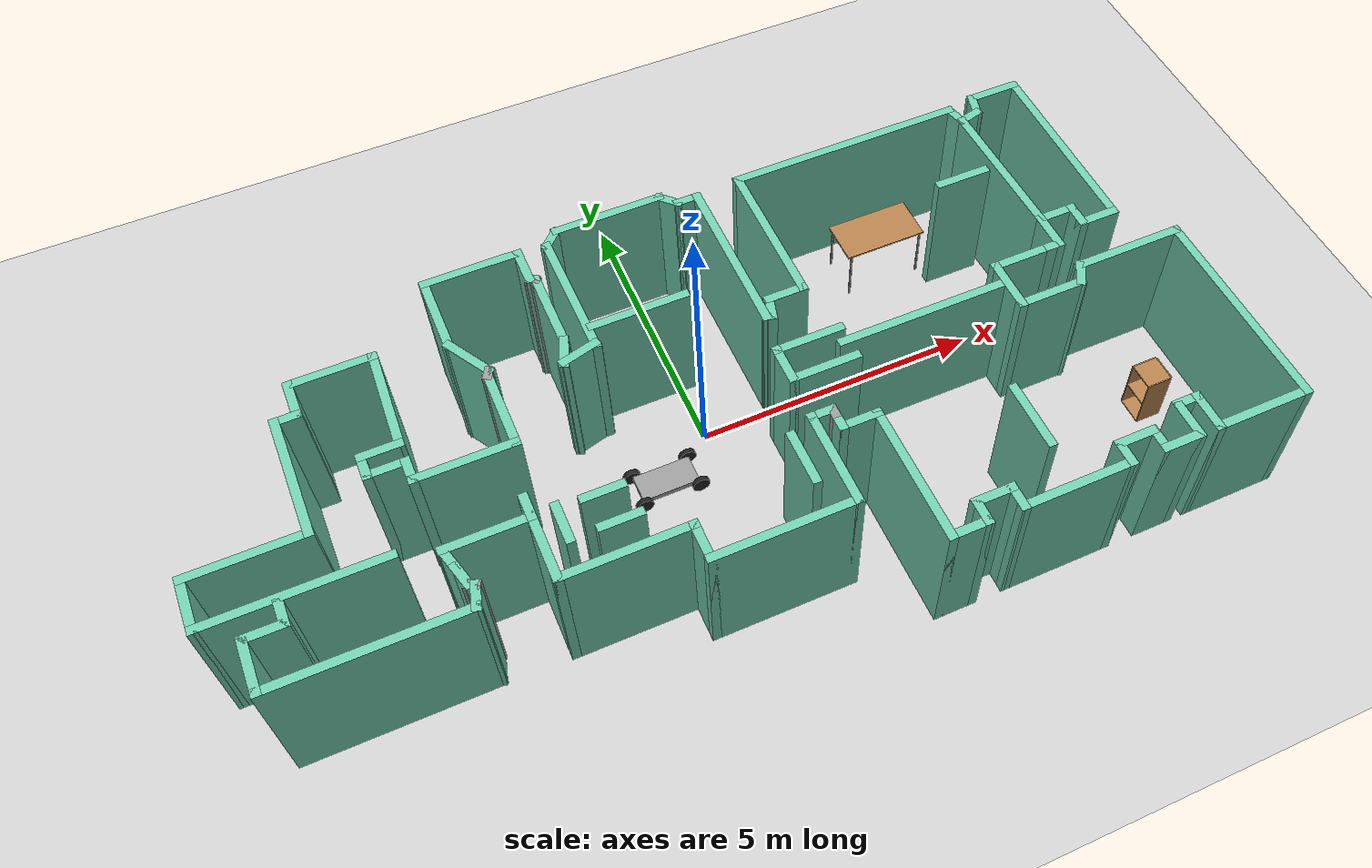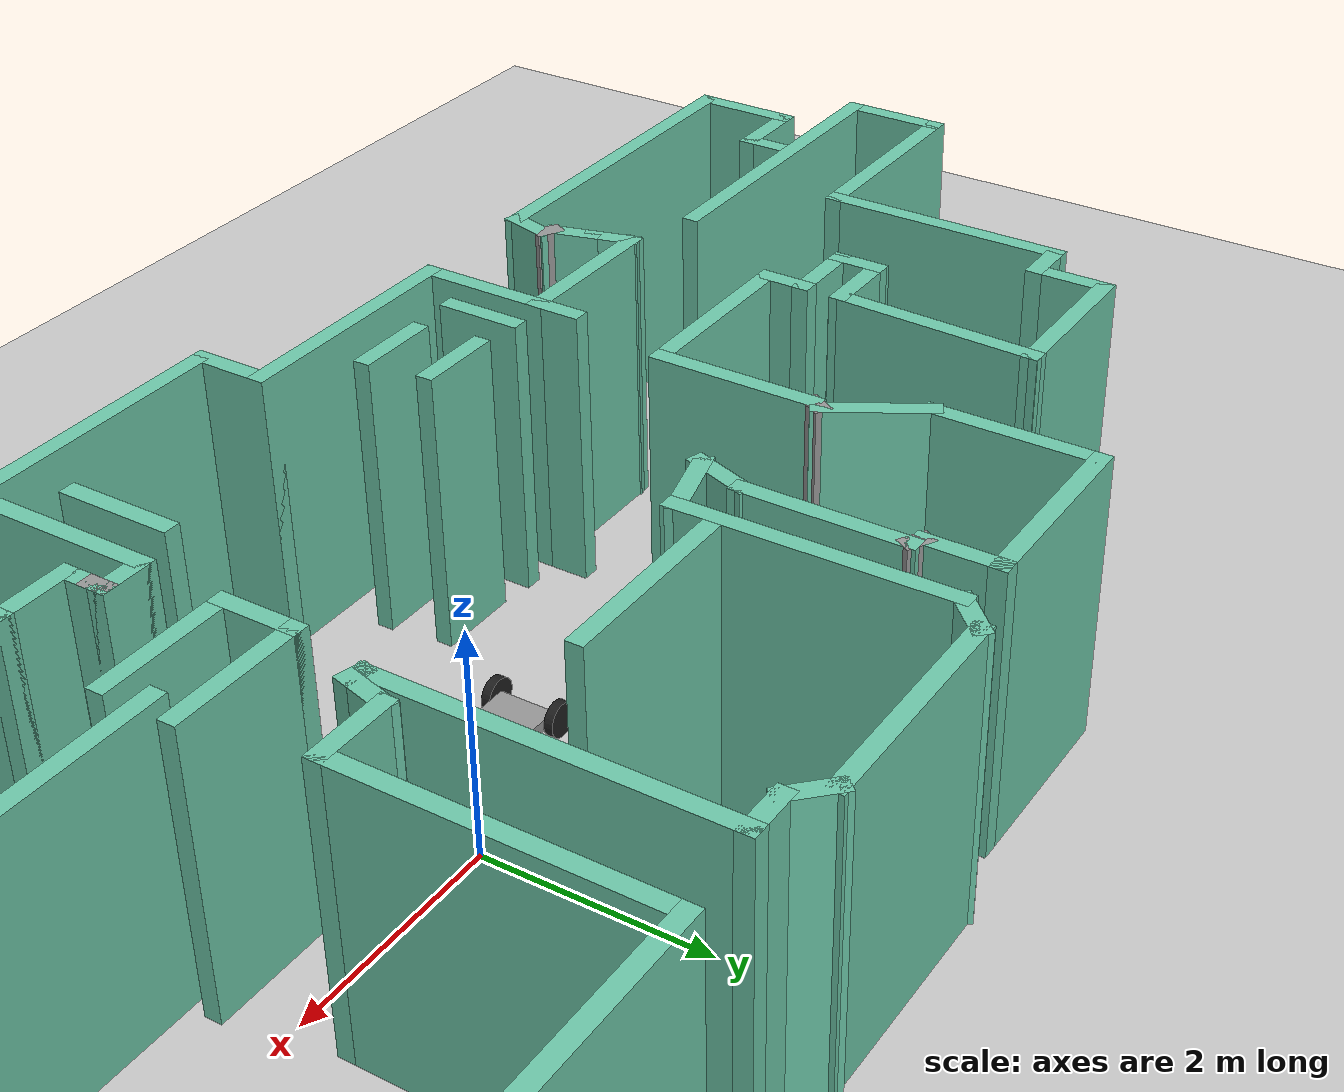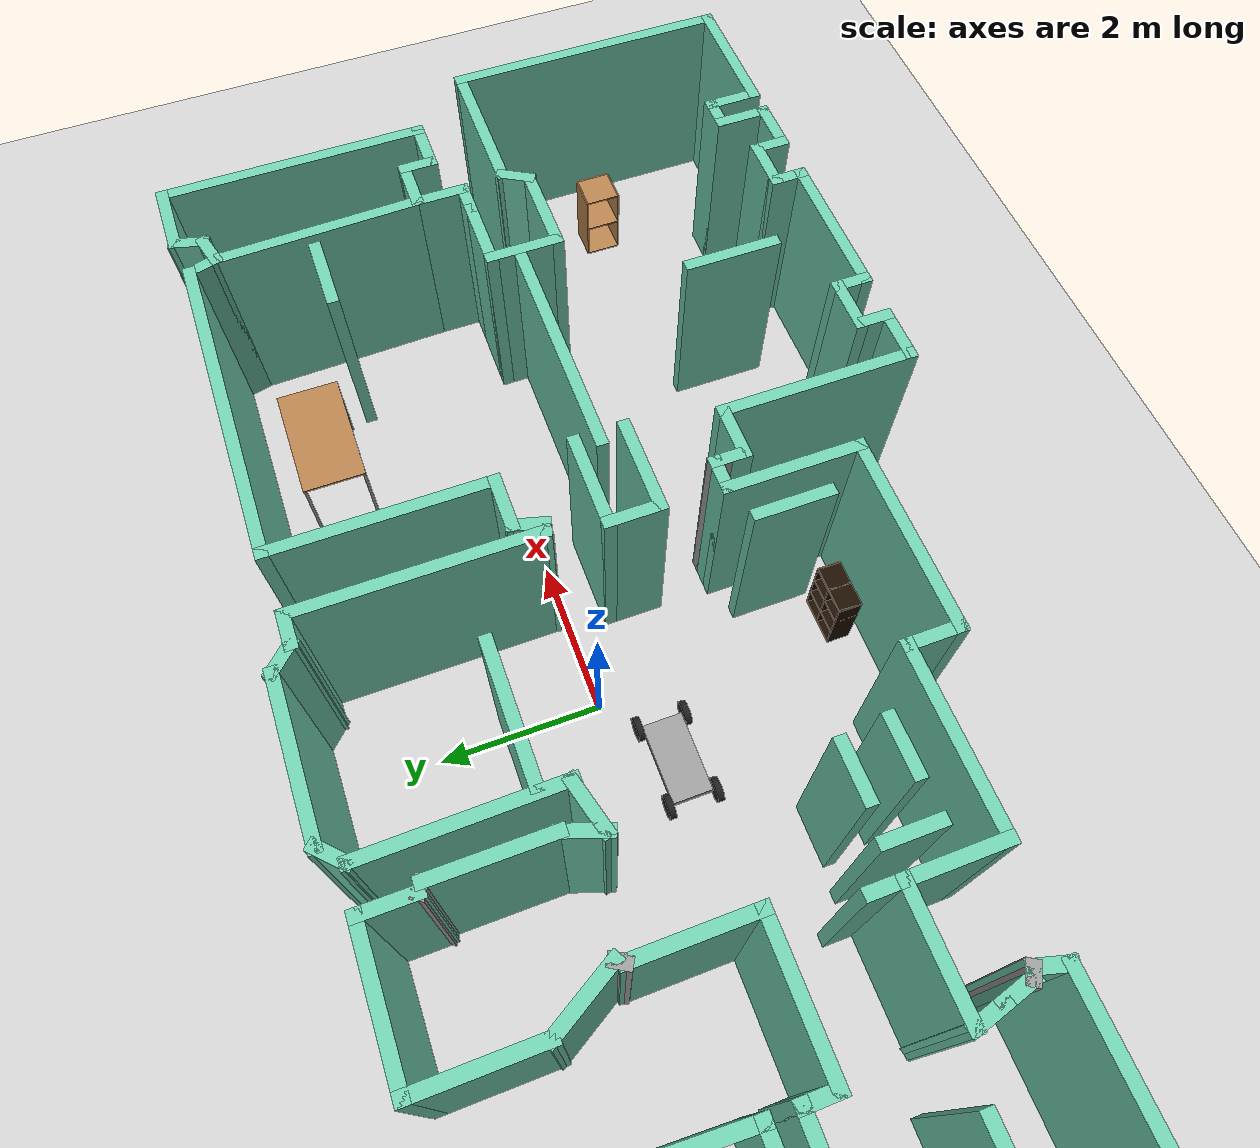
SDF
<sdf version="1.6">
 <world name="default">
  <light name="sun" type="directional">
   <pose>0 0 10 0 -0 0</pose>
   <diffuse>0.8 0.8 0.8 1</diffuse>
   <specular>0.2 0.2 0.2 1</specular>
   <attenuation>
    <range>1000</range>
    <constant>0.9</constant>
    <linear>0.01</linear>
    <quadratic>0.001</quadratic>
   </attenuation>
   <direction>-0.5 0.1 -0.9</direction>
  </light>
  <model name="ground_plane">
   <static>1</static>
   <link name="link">
    <collision name="collision">
     <geometry><plane><normal>0 0 1</normal><size>100 100</size></plane></geometry>
     <surface>
      <contact><collide_bitmask>65535</collide_bitmask></contact>
      <friction><ode><mu>100</mu><mu2>50</mu2></ode></friction>
     </surface>
    </collision>
    <visual name="visual">
     <cast_shadows>0</cast_shadows>
     <geometry><plane><normal>0 0 1</normal><size>100 100</size></plane></geometry>
     <material>
      <script><uri>file://media/materials/scripts/gazebo.material</uri><name>Gazebo/Grey</name></script>
     </material>
    </visual>
   </link>
  </model>
  <gravity>0 0 -9.8</gravity>
  <magnetic_field>6e-06 2.3e-05 -4.2e-05</magnetic_field>
  <atmosphere type="adiabatic"/>
  <physics name="default_physics" default="0" type="ode">
   <max_step_size>0.001</max_step_size>
   <real_time_factor>1</real_time_factor>
   <real_time_update_rate>1000</real_time_update_rate>
  </physics>
  <scene><ambient>0.4 0.4 0.4 1</ambient><background>0.7 0.7 0.7 1</background><shadows>1</shadows></scene>
  <audio><device>default</device></audio>
  <spherical_coordinates>
   <surface_model>EARTH_WGS84</surface_model>
   <latitude_deg>0</latitude_deg>
   <longitude_deg>0</longitude_deg>
   <elevation>0</elevation>
   <heading_deg>0</heading_deg>
  </spherical_coordinates>
  <model name="map_8">
   <pose>-0.03403 -0.65715 0 0 -0 0</pose>
   <link name="Wall_0">
    <collision name="Wall_0_Collision">
     <geometry><box><size>1.5 0.15 2.5</size></box></geometry>
     <pose>0 0 1.25 0 -0 0</pose>
    </collision>
    <visual name="Wall_0_Visual">
     <pose>0 0 1.25 0 -0 0</pose>
     <geometry><box><size>1.5 0.15 2.5</size></box></geometry>
     <material>
      <script><uri>file://media/materials/scripts/gazebo.material</uri><name>Gazebo/Grey</name></script>
      <ambient>0.435294 0.796078 0.67451 1</ambient>
     </material>
     <meta><layer>0</layer></meta>
    </visual>
    <pose>-5.35674 2.63095 0 0 -0 3.14159</pose>
   </link>
   <link name="Wall_1">
    <collision name="Wall_1_Collision">
     <geometry><box><size>0.75 0.15 2.5</size></box></geometry>
     <pose>0 0 1.25 0 -0 0</pose>
    </collision>
    <visual name="Wall_1_Visual">
     <pose>0 0 1.25 0 -0 0</pose>
     <geometry><box><size>0.75 0.15 2.5</size></box></geometry>
     <material>
      <script><uri>file://media/materials/scripts/gazebo.material</uri><name>Gazebo/Grey</name></script>
      <ambient>0.435294 0.796078 0.67451 1</ambient>
     </material>
     <meta><layer>0</layer></meta>
    </visual>
    <pose>-6.03174 2.33095 0 0 -0 -1.5708</pose>
   </link>
   <link name="Wall_100">
    <collision name="Wall_100_Collision">
     <geometry><box><size>0.5 0.15 2.5</size></box></geometry>
     <pose>0 0 1.25 0 -0 0</pose>
    </collision>
    <visual name="Wall_100_Visual">
     <pose>0 0 1.25 0 -0 0</pose>
     <geometry><box><size>0.5 0.15 2.5</size></box></geometry>
     <material>
      <script><uri>file://media/materials/scripts/gazebo.material</uri><name>Gazebo/Grey</name></script>
      <ambient>0.435294 0.796078 0.67451 1</ambient>
     </material>
     <meta><layer>0</layer></meta>
    </visual>
    <pose>-4.76082 0.357873 0 0 -0 1.5708</pose>
   </link>
   <link name="Wall_101">
    <collision name="Wall_101_Collision">
     <geometry><box><size>0.75 0.15 2.5</size></box></geometry>
     <pose>0 0 1.25 0 -0 0</pose>
    </collision>
    <visual name="Wall_101_Visual">
     <pose>0 0 1.25 0 -0 0</pose>
     <geometry><box><size>0.75 0.15 2.5</size></box></geometry>
     <material>
      <script><uri>file://media/materials/scripts/gazebo.material</uri><name>Gazebo/Grey</name></script>
      <ambient>0.435294 0.796078 0.67451 1</ambient>
     </material>
     <meta><layer>0</layer></meta>
    </visual>
    <pose>-5.06081 0.532873 0 0 -0 3.14159</pose>
   </link>
   <link name="Wall_102">
    <collision name="Wall_102_Collision">
     <geometry><box><size>0.5 0.15 2.5</size></box></geometry>
     <pose>0 0 1.25 0 -0 0</pose>
    </collision>
    <visual name="Wall_102_Visual">
     <pose>0 0 1.25 0 -0 0</pose>
     <geometry><box><size>0.5 0.15 2.5</size></box></geometry>
     <material>
      <script><uri>file://media/materials/scripts/gazebo.material</uri><name>Gazebo/Grey</name></script>
      <ambient>0.435294 0.796078 0.67451 1</ambient>
     </material>
     <meta><layer>0</layer></meta>
    </visual>
    <pose>-5.36081 0.707873 0 0 -0 1.5708</pose>
   </link>
   <link name="Wall_103">
    <collision name="Wall_103_Collision">
     <geometry><box><size>0.75 0.15 2.5</size></box></geometry>
     <pose>0 0 1.25 0 -0 0</pose>
    </collision>
    <visual name="Wall_103_Visual">
     <pose>0 0 1.25 0 -0 0</pose>
     <geometry><box><size>0.75 0.15 2.5</size></box></geometry>
     <material>
      <script><uri>file://media/materials/scripts/gazebo.material</uri><name>Gazebo/Grey</name></script>
      <ambient>0.435294 0.796078 0.67451 1</ambient>
     </material>
     <meta><layer>0</layer></meta>
    </visual>
    <pose>-5.06081 0.882873 0 0 -0 0</pose>
   </link>
   <link name="Wall_104">
    <collision name="Wall_104_Collision">
     <geometry><box><size>1.89986 0.15 2.5</size></box></geometry>
     <pose>0 0 1.25 0 -0 0</pose>
    </collision>
    <visual name="Wall_104_Visual">
     <pose>0 0 1.25 0 -0 0</pose>
     <geometry><box><size>1.89986 0.15 2.5</size></box></geometry>
     <material>
      <script><uri>file://media/materials/scripts/gazebo.material</uri><name>Gazebo/Grey</name></script>
      <ambient>0.435294 0.796078 0.67451 1</ambient>
     </material>
     <meta><layer>0</layer></meta>
    </visual>
    <pose>-4.72128 1.75691 0 0 -0 1.52559</pose>
   </link>
   <link name="Wall_106">
    <collision name="Wall_106_Collision">
     <geometry><box><size>1 0.15 2.5</size></box></geometry>
     <pose>0 0 1.25 0 -0 0</pose>
    </collision>
    <visual name="Wall_106_Visual">
     <pose>0 0 1.25 0 -0 0</pose>
     <geometry><box><size>1 0.15 2.5</size></box></geometry>
     <material>
      <script><uri>file://media/materials/scripts/gazebo.material</uri><name>Gazebo/Grey</name></script>
      <ambient>0.435294 0.796078 0.67451 1</ambient>
     </material>
     <meta><layer>0</layer></meta>
    </visual>
    <pose>5.57376 2.19147 0 0 -0 0</pose>
   </link>
   <link name="Wall_108">
    <collision name="Wall_108_Collision">
     <geometry><box><size>2.72254 0.15 2.5</size></box></geometry>
     <pose>0 0 1.25 0 -0 0</pose>
    </collision>
    <visual name="Wall_108_Visual">
     <pose>0 0 1.25 0 -0 0</pose>
     <geometry><box><size>2.72254 0.15 2.5</size></box></geometry>
     <material>
      <script><uri>file://media/materials/scripts/gazebo.material</uri><name>Gazebo/Grey</name></script>
      <ambient>0.435294 0.796078 0.67451 1</ambient>
     </material>
     <meta><layer>0</layer></meta>
    </visual>
    <pose>6.26741 2.09623 0 0 -0 -1.54021</pose>
   </link>
   <link name="Wall_11">
    <collision name="Wall_11_Collision">
     <geometry><box><size>0.75 0.15 2.5</size></box></geometry>
     <pose>0 0 1.25 0 -0 0</pose>
    </collision>
    <visual name="Wall_11_Visual">
     <pose>0 0 1.25 0 -0 0</pose>
     <geometry><box><size>0.75 0.15 2.5</size></box></geometry>
     <material>
      <script><uri>file://media/materials/scripts/gazebo.material</uri><name>Gazebo/Grey</name></script>
      <ambient>0.435294 0.796078 0.67451 1</ambient>
     </material>
     <meta><layer>0</layer></meta>
    </visual>
    <pose>-7.34107 -1.35055 0 0 -0 3.14159</pose>
   </link>
   <link name="Wall_113">
    <collision name="Wall_113_Collision">
     <geometry><box><size>1.75 0.15 2.5</size></box></geometry>
     <pose>0 0 1.25 0 -0 0</pose>
    </collision>
    <visual name="Wall_113_Visual">
     <pose>0 0 1.25 0 -0 0</pose>
     <geometry><box><size>1.75 0.15 2.5</size></box></geometry>
     <material>
      <script><uri>file://media/materials/scripts/gazebo.material</uri><name>Gazebo/Grey</name></script>
      <ambient>0.435294 0.796078 0.67451 1</ambient>
     </material>
     <meta><layer>0</layer></meta>
    </visual>
    <pose>-0.554925 1.77512 0 0 -0 3.14159</pose>
   </link>
   <link name="Wall_115">
    <collision name="Wall_115_Collision">
     <geometry><box><size>3 0.15 2.5</size></box></geometry>
     <pose>0 0 1.25 0 -0 0</pose>
    </collision>
    <visual name="Wall_115_Visual">
     <pose>0 0 1.25 0 -0 0</pose>
     <geometry><box><size>3 0.15 2.5</size></box></geometry>
     <material>
      <script><uri>file://media/materials/scripts/gazebo.material</uri><name>Gazebo/Grey</name></script>
      <ambient>0.435294 0.796078 0.67451 1</ambient>
     </material>
     <meta><layer>0</layer></meta>
    </visual>
    <pose>3.56185 -0.144722 0 0 -0 3.14159</pose>
   </link>
   <link name="Wall_118">
    <collision name="Wall_118_Collision">
     <geometry><box><size>0.75 0.15 2.5</size></box></geometry>
     <pose>0 0 1.25 0 -0 0</pose>
    </collision>
    <visual name="Wall_118_Visual">
     <pose>0 0 1.25 0 -0 0</pose>
     <geometry><box><size>0.75 0.15 2.5</size></box></geometry>
     <material>
      <script><uri>file://media/materials/scripts/gazebo.material</uri><name>Gazebo/Grey</name></script>
      <ambient>0.435294 0.796078 0.67451 1</ambient>
     </material>
     <meta><layer>0</layer></meta>
    </visual>
    <pose>1.12404 -0.167155 0 0 -0 -1.5708</pose>
   </link>
   <link name="Wall_119">
    <collision name="Wall_119_Collision">
     <geometry><box><size>1.25 0.15 2.5</size></box></geometry>
     <pose>0 0 1.25 0 -0 0</pose>
    </collision>
    <visual name="Wall_119_Visual">
     <pose>0 0 1.25 0 -0 0</pose>
     <geometry><box><size>1.25 0.15 2.5</size></box></geometry>
     <material>
      <script><uri>file://media/materials/scripts/gazebo.material</uri><name>Gazebo/Grey</name></script>
      <ambient>0.435294 0.796078 0.67451 1</ambient>
     </material>
     <meta><layer>0</layer></meta>
    </visual>
    <pose>1.67404 -0.467155 0 0 -0 0</pose>
   </link>
   <link name="Wall_12">
    <collision name="Wall_12_Collision">
     <geometry><box><size>1 0.15 2.5</size></box></geometry>
     <pose>0 0 1.25 0 -0 0</pose>
    </collision>
    <visual name="Wall_12_Visual">
     <pose>0 0 1.25 0 -0 0</pose>
     <geometry><box><size>1 0.15 2.5</size></box></geometry>
     <material>
      <script><uri>file://media/materials/scripts/gazebo.material</uri><name>Gazebo/Grey</name></script>
      <ambient>0.435294 0.796078 0.67451 1</ambient>
     </material>
     <meta><layer>0</layer></meta>
    </visual>
    <pose>-7.64107 -1.77555 0 0 -0 -1.5708</pose>
   </link>
   <link name="Wall_121">
    <collision name="Wall_121_Collision">
     <geometry><box><size>1.25 0.15 2.5</size></box></geometry>
     <pose>0 0 1.25 0 -0 0</pose>
    </collision>
    <visual name="Wall_121_Visual">
     <pose>0 0 1.25 0 -0 0</pose>
     <geometry><box><size>1.25 0.15 2.5</size></box></geometry>
     <material>
      <script><uri>file://media/materials/scripts/gazebo.material</uri><name>Gazebo/Grey</name></script>
      <ambient>0.435294 0.796078 0.67451 1</ambient>
     </material>
     <meta><layer>0</layer></meta>
    </visual>
    <pose>1.67404 0.132845 0 0 -0 0</pose>
   </link>
   <link name="Wall_123">
    <collision name="Wall_123_Collision">
     <geometry><box><size>1.25 0.15 2.5</size></box></geometry>
     <pose>0 0 1.25 0 -0 0</pose>
    </collision>
    <visual name="Wall_123_Visual">
     <pose>0 0 1.25 0 -0 0</pose>
     <geometry><box><size>1.25 0.15 2.5</size></box></geometry>
     <material>
      <script><uri>file://media/materials/scripts/gazebo.material</uri><name>Gazebo/Grey</name></script>
      <ambient>0.435294 0.796078 0.67451 1</ambient>
     </material>
     <meta><layer>0</layer></meta>
    </visual>
    <pose>4.15415 -2.59143 0 0 -0 -1.5708</pose>
   </link>
   <link name="Wall_125">
    <collision name="Wall_125_Collision">
     <geometry><box><size>0.75 0.15 2.5</size></box></geometry>
     <pose>0 0 1.25 0 -0 0</pose>
    </collision>
    <visual name="Wall_125_Visual">
     <pose>0 0 1.25 0 -0 0</pose>
     <geometry><box><size>0.75 0.15 2.5</size></box></geometry>
     <material>
      <script><uri>file://media/materials/scripts/gazebo.material</uri><name>Gazebo/Grey</name></script>
      <ambient>0.435294 0.796078 0.67451 1</ambient>
     </material>
     <meta><layer>0</layer></meta>
    </visual>
    <pose>-2.99321 -1.41621 0 0 -0 -1.5708</pose>
   </link>
   <link name="Wall_128">
    <collision name="Wall_128_Collision">
     <geometry><box><size>0.75 0.15 2.5</size></box></geometry>
     <pose>0 0 1.25 0 -0 0</pose>
    </collision>
    <visual name="Wall_128_Visual">
     <pose>0 0 1.25 0 -0 0</pose>
     <geometry><box><size>0.75 0.15 2.5</size></box></geometry>
     <material>
      <script><uri>file://media/materials/scripts/gazebo.material</uri><name>Gazebo/Grey</name></script>
      <ambient>0.435294 0.796078 0.67451 1</ambient>
     </material>
     <meta><layer>0</layer></meta>
    </visual>
    <pose>-2.27686 -1.16247 0 0 -0 0</pose>
   </link>
   <link name="Wall_13">
    <collision name="Wall_13_Collision">
     <geometry><box><size>3.25 0.15 2.5</size></box></geometry>
     <pose>0 0 1.25 0 -0 0</pose>
    </collision>
    <visual name="Wall_13_Visual">
     <pose>0 0 1.25 0 -0 0</pose>
     <geometry><box><size>3.25 0.15 2.5</size></box></geometry>
     <material>
      <script><uri>file://media/materials/scripts/gazebo.material</uri><name>Gazebo/Grey</name></script>
      <ambient>0.435294 0.796078 0.67451 1</ambient>
     </material>
     <meta><layer>0</layer></meta>
    </visual>
    <pose>-6.09107 -2.20056 0 0 -0 0</pose>
   </link>
   <link name="Wall_130">
    <collision name="Wall_130_Collision">
     <geometry><box><size>0.75 0.15 2.5</size></box></geometry>
     <pose>0 0 1.25 0 -0 0</pose>
    </collision>
    <visual name="Wall_130_Visual">
     <pose>0 0 1.25 0 -0 0</pose>
     <geometry><box><size>0.75 0.15 2.5</size></box></geometry>
     <material>
      <script><uri>file://media/materials/scripts/gazebo.material</uri><name>Gazebo/Grey</name></script>
      <ambient>0.435294 0.796078 0.67451 1</ambient>
     </material>
     <meta><layer>0</layer></meta>
    </visual>
    <pose>-2.20747 -1.7176 0 0 -0 0</pose>
   </link>
   <link name="Wall_132">
    <collision name="Wall_132_Collision">
     <geometry><box><size>1 0.15 2.5</size></box></geometry>
     <pose>0 0 1.25 0 -0 0</pose>
    </collision>
    <visual name="Wall_132_Visual">
     <pose>0 0 1.25 0 -0 0</pose>
     <geometry><box><size>1 0.15 2.5</size></box></geometry>
     <material>
      <script><uri>file://media/materials/scripts/gazebo.material</uri><name>Gazebo/Grey</name></script>
      <ambient>0.435294 0.796078 0.67451 1</ambient>
     </material>
     <meta><layer>0</layer></meta>
    </visual>
    <pose>0.661426 -1.84191 0 0 -0 -1.5708</pose>
   </link>
   <link name="Wall_14">
    <collision name="Wall_14_Collision">
     <geometry><box><size>0.5 0.15 2.5</size></box></geometry>
     <pose>0 0 1.25 0 -0 0</pose>
    </collision>
    <visual name="Wall_14_Visual">
     <pose>0 0 1.25 0 -0 0</pose>
     <geometry><box><size>0.5 0.15 2.5</size></box></geometry>
     <material>
      <script><uri>file://media/materials/scripts/gazebo.material</uri><name>Gazebo/Grey</name></script>
      <ambient>0.435294 0.796078 0.67451 1</ambient>
     </material>
     <meta><layer>0</layer></meta>
    </visual>
    <pose>-4.49577 -2.03152 0 0 -0 1.309</pose>
   </link>
   <link name="Wall_15">
    <collision name="Wall_15_Collision">
     <geometry><box><size>0.25 0.15 2.5</size></box></geometry>
     <pose>0 0 1.25 0 -0 0</pose>
    </collision>
    <visual name="Wall_15_Visual">
     <pose>0 0 1.25 0 -0 0</pose>
     <geometry><box><size>0.25 0.15 2.5</size></box></geometry>
     <material>
      <script><uri>file://media/materials/scripts/gazebo.material</uri><name>Gazebo/Grey</name></script>
      <ambient>1 1 1 1</ambient>
     </material>
     <meta><layer>0</layer></meta>
    </visual>
    <pose>-4.49378 -1.83748 0 0 -0 2.61799</pose>
   </link>
   <link name="Wall_16">
    <collision name="Wall_16_Collision">
     <geometry><box><size>0.5 0.15 2.5</size></box></geometry>
     <pose>0 0 1.25 0 -0 0</pose>
    </collision>
    <visual name="Wall_16_Visual">
     <pose>0 0 1.25 0 -0 0</pose>
     <geometry><box><size>0.5 0.15 2.5</size></box></geometry>
     <material>
      <script><uri>file://media/materials/scripts/gazebo.material</uri><name>Gazebo/Grey</name></script>
      <ambient>0.435294 0.796078 0.67451 1</ambient>
     </material>
     <meta><layer>0</layer></meta>
    </visual>
    <pose>-4.58237 -1.64344 0 0 -0 1.8326</pose>
   </link>
   <link name="Wall_17">
    <collision name="Wall_17_Collision">
     <geometry><box><size>0.5 0.15 2.5</size></box></geometry>
     <pose>0 0 1.25 0 -0 0</pose>
    </collision>
    <visual name="Wall_17_Visual">
     <pose>0 0 1.25 0 -0 0</pose>
     <geometry><box><size>0.5 0.15 2.5</size></box></geometry>
     <material>
      <script><uri>file://media/materials/scripts/gazebo.material</uri><name>Gazebo/Grey</name></script>
      <ambient>0.435294 0.796078 0.67451 1</ambient>
     </material>
     <meta><layer>0</layer></meta>
    </visual>
    <pose>-4.67296 -1.30537 0 0 -0 1.8326</pose>
   </link>
   <link name="Wall_2">
    <collision name="Wall_2_Collision">
     <geometry><box><size>0.5 0.15 2.5</size></box></geometry>
     <pose>0 0 1.25 0 -0 0</pose>
    </collision>
    <visual name="Wall_2_Visual">
     <pose>0 0 1.25 0 -0 0</pose>
     <geometry><box><size>0.5 0.15 2.5</size></box></geometry>
     <material>
      <script><uri>file://media/materials/scripts/gazebo.material</uri><name>Gazebo/Grey</name></script>
      <ambient>0.435294 0.796078 0.67451 1</ambient>
     </material>
     <meta><layer>0</layer></meta>
    </visual>
    <pose>-6.20674 2.03095 0 0 -0 3.14159</pose>
   </link>
   <link name="Wall_20">
    <collision name="Wall_20_Collision">
     <geometry><box><size>1.5 0.15 2.5</size></box></geometry>
     <pose>0 0 1.25 0 -0 0</pose>
    </collision>
    <visual name="Wall_20_Visual">
     <pose>0 0 1.25 0 -0 0</pose>
     <geometry><box><size>1.5 0.15 2.5</size></box></geometry>
     <material>
      <script><uri>file://media/materials/scripts/gazebo.material</uri><name>Gazebo/Grey</name></script>
      <ambient>0.435294 0.796078 0.67451 1</ambient>
     </material>
     <meta><layer>0</layer></meta>
    </visual>
    <pose>-4.04326 -1.13633 0 0 -0 0</pose>
   </link>
   <link name="Wall_21">
    <collision name="Wall_21_Collision">
     <geometry><box><size>0.5 0.15 2.5</size></box></geometry>
     <pose>0 0 1.25 0 -0 0</pose>
    </collision>
    <visual name="Wall_21_Visual">
     <pose>0 0 1.25 0 -0 0</pose>
     <geometry><box><size>0.5 0.15 2.5</size></box></geometry>
     <material>
      <script><uri>file://media/materials/scripts/gazebo.material</uri><name>Gazebo/Grey</name></script>
      <ambient>0.435294 0.796078 0.67451 1</ambient>
     </material>
     <meta><layer>0</layer></meta>
    </visual>
    <pose>-3.36825 -0.961333 0 0 -0 1.5708</pose>
   </link>
   <link name="Wall_25">
    <collision name="Wall_25_Collision">
     <geometry><box><size>1.25 0.15 2.5</size></box></geometry>
     <pose>0 0 1.25 0 -0 0</pose>
    </collision>
    <visual name="Wall_25_Visual">
     <pose>0 0 1.25 0 -0 0</pose>
     <geometry><box><size>1.25 0.15 2.5</size></box></geometry>
     <material>
      <script><uri>file://media/materials/scripts/gazebo.material</uri><name>Gazebo/Grey</name></script>
      <ambient>0.435294 0.796078 0.67451 1</ambient>
     </material>
     <meta><layer>0</layer></meta>
    </visual>
    <pose>-3.36825 -1.68633 0 0 -0 -1.5708</pose>
   </link>
   <link name="Wall_26">
    <collision name="Wall_26_Collision">
     <geometry><box><size>2.25 0.15 2.5</size></box></geometry>
     <pose>0 0 1.25 0 -0 0</pose>
    </collision>
    <visual name="Wall_26_Visual">
     <pose>0 0 1.25 0 -0 0</pose>
     <geometry><box><size>2.25 0.15 2.5</size></box></geometry>
     <material>
      <script><uri>file://media/materials/scripts/gazebo.material</uri><name>Gazebo/Grey</name></script>
      <ambient>0.435294 0.796078 0.67451 1</ambient>
     </material>
     <meta><layer>0</layer></meta>
    </visual>
    <pose>-2.31826 -2.23633 0 0 -0 0</pose>
   </link>
   <link name="Wall_27">
    <collision name="Wall_27_Collision">
     <geometry><box><size>0.75 0.15 2.5</size></box></geometry>
     <pose>0 0 1.25 0 -0 0</pose>
    </collision>
    <visual name="Wall_27_Visual">
     <pose>0 0 1.25 0 -0 0</pose>
     <geometry><box><size>0.75 0.15 2.5</size></box></geometry>
     <material>
      <script><uri>file://media/materials/scripts/gazebo.material</uri><name>Gazebo/Grey</name></script>
      <ambient>0.435294 0.796078 0.67451 1</ambient>
     </material>
     <meta><layer>0</layer></meta>
    </visual>
    <pose>-1.26825 -2.53633 0 0 -0 -1.5708</pose>
   </link>
   <link name="Wall_3">
    <collision name="Wall_3_Collision">
     <geometry><box><size>2.25 0.15 2.5</size></box></geometry>
     <pose>0 0 1.25 0 -0 0</pose>
    </collision>
    <visual name="Wall_3_Visual">
     <pose>0 0 1.25 0 -0 0</pose>
     <geometry><box><size>2.25 0.15 2.5</size></box></geometry>
     <material>
      <script><uri>file://media/materials/scripts/gazebo.material</uri><name>Gazebo/Grey</name></script>
      <ambient>0.435294 0.796078 0.67451 1</ambient>
     </material>
     <meta><layer>0</layer></meta>
    </visual>
    <pose>-6.38174 0.980951 0 0 -0 -1.5708</pose>
   </link>
   <link name="Wall_30">
    <collision name="Wall_30_Collision">
     <geometry><box><size>2.5 0.15 2.5</size></box></geometry>
     <pose>0 0 1.25 0 -0 0</pose>
    </collision>
    <visual name="Wall_30_Visual">
     <pose>0 0 1.25 0 -0 0</pose>
     <geometry><box><size>2.5 0.15 2.5</size></box></geometry>
     <material>
      <script><uri>file://media/materials/scripts/gazebo.material</uri><name>Gazebo/Grey</name></script>
      <ambient>0.435294 0.796078 0.67451 1</ambient>
     </material>
     <meta><layer>0</layer></meta>
    </visual>
    <pose>-0.093255 -2.83633 0 0 -0 0</pose>
   </link>
   <link name="Wall_31">
    <collision name="Wall_31_Collision">
     <geometry><box><size>1.75 0.15 2.5</size></box></geometry>
     <pose>0 0 1.25 0 -0 0</pose>
    </collision>
    <visual name="Wall_31_Visual">
     <pose>0 0 1.25 0 -0 0</pose>
     <geometry><box><size>1.75 0.15 2.5</size></box></geometry>
     <material>
      <script><uri>file://media/materials/scripts/gazebo.material</uri><name>Gazebo/Grey</name></script>
      <ambient>0.435294 0.796078 0.67451 1</ambient>
     </material>
     <meta><layer>0</layer></meta>
    </visual>
    <pose>1.08174 -2.03633 0 0 -0 1.5708</pose>
   </link>
   <link name="Wall_32">
    <collision name="Wall_32_Collision">
     <geometry><box><size>0.5 0.15 2.5</size></box></geometry>
     <pose>0 0 1.25 0 -0 0</pose>
    </collision>
    <visual name="Wall_32_Visual">
     <pose>0 0 1.25 0 -0 0</pose>
     <geometry><box><size>0.5 0.15 2.5</size></box></geometry>
     <material>
      <script><uri>file://media/materials/scripts/gazebo.material</uri><name>Gazebo/Grey</name></script>
      <ambient>0.435294 0.796078 0.67451 1</ambient>
     </material>
     <meta><layer>0</layer></meta>
    </visual>
    <pose>1.25675 -1.23633 0 0 -0 0</pose>
   </link>
   <link name="Wall_33">
    <collision name="Wall_33_Collision">
     <geometry><box><size>0.25 0.15 2.5</size></box></geometry>
     <pose>0 0 1.25 0 -0 0</pose>
    </collision>
    <visual name="Wall_33_Visual">
     <pose>0 0 1.25 0 -0 0</pose>
     <geometry><box><size>0.25 0.15 2.5</size></box></geometry>
     <material>
      <script><uri>file://media/materials/scripts/gazebo.material</uri><name>Gazebo/Grey</name></script>
      <ambient>1 1 1 1</ambient>
     </material>
     <meta><layer>0</layer></meta>
    </visual>
    <pose>1.43175 -1.28633 0 0 -0 -1.5708</pose>
   </link>
   <link name="Wall_36">
    <collision name="Wall_36_Collision">
     <geometry><box><size>0.5 0.15 2.5</size></box></geometry>
     <pose>0 0 1.25 0 -0 0</pose>
    </collision>
    <visual name="Wall_36_Visual">
     <pose>0 0 1.25 0 -0 0</pose>
     <geometry><box><size>0.5 0.15 2.5</size></box></geometry>
     <material>
      <script><uri>file://media/materials/scripts/gazebo.material</uri><name>Gazebo/Grey</name></script>
      <ambient>0.435294 0.796078 0.67451 1</ambient>
     </material>
     <meta><layer>0</layer></meta>
    </visual>
    <pose>1.43175 -1.41133 0 0 -0 -1.5708</pose>
   </link>
   <link name="Wall_39">
    <collision name="Wall_39_Collision">
     <geometry><box><size>0.75 0.15 2.5</size></box></geometry>
     <pose>0 0 1.25 0 -0 0</pose>
    </collision>
    <visual name="Wall_39_Visual">
     <pose>0 0 1.25 0 -0 0</pose>
     <geometry><box><size>0.75 0.15 2.5</size></box></geometry>
     <material>
      <script><uri>file://media/materials/scripts/gazebo.material</uri><name>Gazebo/Grey</name></script>
      <ambient>0.435294 0.796078 0.67451 1</ambient>
     </material>
     <meta><layer>0</layer></meta>
    </visual>
    <pose>1.73175 -1.58633 0 0 -0 0</pose>
   </link>
   <link name="Wall_4">
    <collision name="Wall_4_Collision">
     <geometry><box><size>2 0.15 2.5</size></box></geometry>
     <pose>0 0 1.25 0 -0 0</pose>
    </collision>
    <visual name="Wall_4_Visual">
     <pose>0 0 1.25 0 -0 0</pose>
     <geometry><box><size>2 0.15 2.5</size></box></geometry>
     <material>
      <script><uri>file://media/materials/scripts/gazebo.material</uri><name>Gazebo/Grey</name></script>
      <ambient>0.435294 0.796078 0.67451 1</ambient>
     </material>
     <meta><layer>0</layer></meta>
    </visual>
    <pose>-7.30674 -0.069049 0 0 -0 3.14159</pose>
   </link>
   <link name="Wall_40">
    <collision name="Wall_40_Collision">
     <geometry><box><size>2.5 0.15 2.5</size></box></geometry>
     <pose>0 0 1.25 0 -0 0</pose>
    </collision>
    <visual name="Wall_40_Visual">
     <pose>0 0 1.25 0 -0 0</pose>
     <geometry><box><size>2.5 0.15 2.5</size></box></geometry>
     <material>
      <script><uri>file://media/materials/scripts/gazebo.material</uri><name>Gazebo/Grey</name></script>
      <ambient>0.435294 0.796078 0.67451 1</ambient>
     </material>
     <meta><layer>0</layer></meta>
    </visual>
    <pose>2.03174 -2.76133 0 0 -0 -1.5708</pose>
   </link>
   <link name="Wall_41">
    <collision name="Wall_41_Collision">
     <geometry><box><size>0.75 0.15 2.5</size></box></geometry>
     <pose>0 0 1.25 0 -0 0</pose>
    </collision>
    <visual name="Wall_41_Visual">
     <pose>0 0 1.25 0 -0 0</pose>
     <geometry><box><size>0.75 0.15 2.5</size></box></geometry>
     <material>
      <script><uri>file://media/materials/scripts/gazebo.material</uri><name>Gazebo/Grey</name></script>
      <ambient>0.435294 0.796078 0.67451 1</ambient>
     </material>
     <meta><layer>0</layer></meta>
    </visual>
    <pose>2.33175 -3.93633 0 0 -0 0</pose>
   </link>
   <link name="Wall_42">
    <collision name="Wall_42_Collision">
     <geometry><box><size>0.5 0.15 2.5</size></box></geometry>
     <pose>0 0 1.25 0 -0 0</pose>
    </collision>
    <visual name="Wall_42_Visual">
     <pose>0 0 1.25 0 -0 0</pose>
     <geometry><box><size>0.5 0.15 2.5</size></box></geometry>
     <material>
      <script><uri>file://media/materials/scripts/gazebo.material</uri><name>Gazebo/Grey</name></script>
      <ambient>0.435294 0.796078 0.67451 1</ambient>
     </material>
     <meta><layer>0</layer></meta>
    </visual>
    <pose>2.63175 -3.76133 0 0 -0 1.5708</pose>
   </link>
   <link name="Wall_43">
    <collision name="Wall_43_Collision">
     <geometry><box><size>0.75 0.15 2.5</size></box></geometry>
     <pose>0 0 1.25 0 -0 0</pose>
    </collision>
    <visual name="Wall_43_Visual">
     <pose>0 0 1.25 0 -0 0</pose>
     <geometry><box><size>0.75 0.15 2.5</size></box></geometry>
     <material>
      <script><uri>file://media/materials/scripts/gazebo.material</uri><name>Gazebo/Grey</name></script>
      <ambient>0.435294 0.796078 0.67451 1</ambient>
     </material>
     <meta><layer>0</layer></meta>
    </visual>
    <pose>2.93174 -3.58633 0 0 -0 0</pose>
   </link>
   <link name="Wall_44">
    <collision name="Wall_44_Collision">
     <geometry><box><size>0.5 0.15 2.5</size></box></geometry>
     <pose>0 0 1.25 0 -0 0</pose>
    </collision>
    <visual name="Wall_44_Visual">
     <pose>0 0 1.25 0 -0 0</pose>
     <geometry><box><size>0.5 0.15 2.5</size></box></geometry>
     <material>
      <script><uri>file://media/materials/scripts/gazebo.material</uri><name>Gazebo/Grey</name></script>
      <ambient>0.435294 0.796078 0.67451 1</ambient>
     </material>
     <meta><layer>0</layer></meta>
    </visual>
    <pose>3.23175 -3.76133 0 0 -0 -1.5708</pose>
   </link>
   <link name="Wall_45">
    <collision name="Wall_45_Collision">
     <geometry><box><size>2 0.15 2.5</size></box></geometry>
     <pose>0 0 1.25 0 -0 0</pose>
    </collision>
    <visual name="Wall_45_Visual">
     <pose>0 0 1.25 0 -0 0</pose>
     <geometry><box><size>2 0.15 2.5</size></box></geometry>
     <material>
      <script><uri>file://media/materials/scripts/gazebo.material</uri><name>Gazebo/Grey</name></script>
      <ambient>0.435294 0.796078 0.67451 1</ambient>
     </material>
     <meta><layer>0</layer></meta>
    </visual>
    <pose>4.15674 -3.93633 0 0 -0 0</pose>
   </link>
   <link name="Wall_46">
    <collision name="Wall_46_Collision">
     <geometry><box><size>0.5 0.15 2.5</size></box></geometry>
     <pose>0 0 1.25 0 -0 0</pose>
    </collision>
    <visual name="Wall_46_Visual">
     <pose>0 0 1.25 0 -0 0</pose>
     <geometry><box><size>0.5 0.15 2.5</size></box></geometry>
     <material>
      <script><uri>file://media/materials/scripts/gazebo.material</uri><name>Gazebo/Grey</name></script>
      <ambient>0.435294 0.796078 0.67451 1</ambient>
     </material>
     <meta><layer>0</layer></meta>
    </visual>
    <pose>5.08174 -3.76133 0 0 -0 1.5708</pose>
   </link>
   <link name="Wall_49">
    <collision name="Wall_49_Collision">
     <geometry><box><size>0.75 0.15 2.5</size></box></geometry>
     <pose>0 0 1.25 0 -0 0</pose>
    </collision>
    <visual name="Wall_49_Visual">
     <pose>0 0 1.25 0 -0 0</pose>
     <geometry><box><size>0.75 0.15 2.5</size></box></geometry>
     <material>
      <script><uri>file://media/materials/scripts/gazebo.material</uri><name>Gazebo/Grey</name></script>
      <ambient>0.435294 0.796078 0.67451 1</ambient>
     </material>
     <meta><layer>0</layer></meta>
    </visual>
    <pose>5.38174 -3.58633 0 0 -0 0</pose>
   </link>
   <link name="Wall_5">
    <collision name="Wall_5_Collision">
     <geometry><box><size>1 0.15 2.5</size></box></geometry>
     <pose>0 0 1.25 0 -0 0</pose>
    </collision>
    <visual name="Wall_5_Visual">
     <pose>0 0 1.25 0 -0 0</pose>
     <geometry><box><size>1 0.15 2.5</size></box></geometry>
     <material>
      <script><uri>file://media/materials/scripts/gazebo.material</uri><name>Gazebo/Grey</name></script>
      <ambient>0.435294 0.796078 0.67451 1</ambient>
     </material>
     <meta><layer>0</layer></meta>
    </visual>
    <pose>-8.23174 -0.494049 0 0 -0 -1.5708</pose>
   </link>
   <link name="Wall_50">
    <collision name="Wall_50_Collision">
     <geometry><box><size>0.5 0.15 2.5</size></box></geometry>
     <pose>0 0 1.25 0 -0 0</pose>
    </collision>
    <visual name="Wall_50_Visual">
     <pose>0 0 1.25 0 -0 0</pose>
     <geometry><box><size>0.5 0.15 2.5</size></box></geometry>
     <material>
      <script><uri>file://media/materials/scripts/gazebo.material</uri><name>Gazebo/Grey</name></script>
      <ambient>0.435294 0.796078 0.67451 1</ambient>
     </material>
     <meta><layer>0</layer></meta>
    </visual>
    <pose>5.68175 -3.76133 0 0 -0 -1.5708</pose>
   </link>
   <link name="Wall_51">
    <collision name="Wall_51_Collision">
     <geometry><box><size>0.75 0.15 2.5</size></box></geometry>
     <pose>0 0 1.25 0 -0 0</pose>
    </collision>
    <visual name="Wall_51_Visual">
     <pose>0 0 1.25 0 -0 0</pose>
     <geometry><box><size>0.75 0.15 2.5</size></box></geometry>
     <material>
      <script><uri>file://media/materials/scripts/gazebo.material</uri><name>Gazebo/Grey</name></script>
      <ambient>0.435294 0.796078 0.67451 1</ambient>
     </material>
     <meta><layer>0</layer></meta>
    </visual>
    <pose>5.98175 -3.93633 0 0 -0 0</pose>
   </link>
   <link name="Wall_52">
    <collision name="Wall_52_Collision">
     <geometry><box><size>0.75 0.15 2.5</size></box></geometry>
     <pose>0 0 1.25 0 -0 0</pose>
    </collision>
    <visual name="Wall_52_Visual">
     <pose>0 0 1.25 0 -0 0</pose>
     <geometry><box><size>0.75 0.15 2.5</size></box></geometry>
     <material>
      <script><uri>file://media/materials/scripts/gazebo.material</uri><name>Gazebo/Grey</name></script>
      <ambient>0.435294 0.796078 0.67451 1</ambient>
     </material>
     <meta><layer>0</layer></meta>
    </visual>
    <pose>6.28174 -3.63633 0 0 -0 1.5708</pose>
   </link>
   <link name="Wall_53">
    <collision name="Wall_53_Collision">
     <geometry><box><size>0.5 0.15 2.5</size></box></geometry>
     <pose>0 0 1.25 0 -0 0</pose>
    </collision>
    <visual name="Wall_53_Visual">
     <pose>0 0 1.25 0 -0 0</pose>
     <geometry><box><size>0.5 0.15 2.5</size></box></geometry>
     <material>
      <script><uri>file://media/materials/scripts/gazebo.material</uri><name>Gazebo/Grey</name></script>
      <ambient>0.435294 0.796078 0.67451 1</ambient>
     </material>
     <meta><layer>0</layer></meta>
    </visual>
    <pose>6.45674 -3.33633 0 0 -0 0</pose>
   </link>
   <link name="Wall_54">
    <collision name="Wall_54_Collision">
     <geometry><box><size>0.75 0.15 2.5</size></box></geometry>
     <pose>0 0 1.25 0 -0 0</pose>
    </collision>
    <visual name="Wall_54_Visual">
     <pose>0 0 1.25 0 -0 0</pose>
     <geometry><box><size>0.75 0.15 2.5</size></box></geometry>
     <material>
      <script><uri>file://media/materials/scripts/gazebo.material</uri><name>Gazebo/Grey</name></script>
      <ambient>0.435294 0.796078 0.67451 1</ambient>
     </material>
     <meta><layer>0</layer></meta>
    </visual>
    <pose>6.63174 -3.63633 0 0 -0 -1.5708</pose>
   </link>
   <link name="Wall_55">
    <collision name="Wall_55_Collision">
     <geometry><box><size>1.75 0.15 2.5</size></box></geometry>
     <pose>0 0 1.25 0 -0 0</pose>
    </collision>
    <visual name="Wall_55_Visual">
     <pose>0 0 1.25 0 -0 0</pose>
     <geometry><box><size>1.75 0.15 2.5</size></box></geometry>
     <material>
      <script><uri>file://media/materials/scripts/gazebo.material</uri><name>Gazebo/Grey</name></script>
      <ambient>0.435294 0.796078 0.67451 1</ambient>
     </material>
     <meta><layer>0</layer></meta>
    </visual>
    <pose>7.43174 -3.93633 0 0 -0 0</pose>
   </link>
   <link name="Wall_56">
    <collision name="Wall_56_Collision">
     <geometry><box><size>3.75 0.15 2.5</size></box></geometry>
     <pose>0 0 1.25 0 -0 0</pose>
    </collision>
    <visual name="Wall_56_Visual">
     <pose>0 0 1.25 0 -0 0</pose>
     <geometry><box><size>3.75 0.15 2.5</size></box></geometry>
     <material>
      <script><uri>file://media/materials/scripts/gazebo.material</uri><name>Gazebo/Grey</name></script>
      <ambient>0.435294 0.796078 0.67451 1</ambient>
     </material>
     <meta><layer>0</layer></meta>
    </visual>
    <pose>8.23175 -2.13633 0 0 -0 1.5708</pose>
   </link>
   <link name="Wall_57">
    <collision name="Wall_57_Collision">
     <geometry><box><size>2 0.15 2.5</size></box></geometry>
     <pose>0 0 1.25 0 -0 0</pose>
    </collision>
    <visual name="Wall_57_Visual">
     <pose>0 0 1.25 0 -0 0</pose>
     <geometry><box><size>2 0.15 2.5</size></box></geometry>
     <material>
      <script><uri>file://media/materials/scripts/gazebo.material</uri><name>Gazebo/Grey</name></script>
      <ambient>0.435294 0.796078 0.67451 1</ambient>
     </material>
     <meta><layer>0</layer></meta>
    </visual>
    <pose>7.30674 -0.336333 0 0 -0 3.14159</pose>
   </link>
   <link name="Wall_6">
    <collision name="Wall_6_Collision">
     <geometry><box><size>3 0.15 2.5</size></box></geometry>
     <pose>0 0 1.25 0 -0 0</pose>
    </collision>
    <visual name="Wall_6_Visual">
     <pose>0 0 1.25 0 -0 0</pose>
     <geometry><box><size>3 0.15 2.5</size></box></geometry>
     <material>
      <script><uri>file://media/materials/scripts/gazebo.material</uri><name>Gazebo/Grey</name></script>
      <ambient>0.435294 0.796078 0.67451 1</ambient>
     </material>
     <meta><layer>0</layer></meta>
    </visual>
    <pose>-6.80674 -0.919049 0 0 -0 0</pose>
   </link>
   <link name="Wall_60">
    <collision name="Wall_60_Collision">
     <geometry><box><size>0.5 0.15 2.5</size></box></geometry>
     <pose>0 0 1.25 0 -0 0</pose>
    </collision>
    <visual name="Wall_60_Visual">
     <pose>0 0 1.25 0 -0 0</pose>
     <geometry><box><size>0.5 0.15 2.5</size></box></geometry>
     <material>
      <script><uri>file://media/materials/scripts/gazebo.material</uri><name>Gazebo/Grey</name></script>
      <ambient>0.435294 0.796078 0.67451 1</ambient>
     </material>
     <meta><layer>0</layer></meta>
    </visual>
    <pose>6.29425 -0.487887 0 0 -0 -2.0944</pose>
   </link>
   <link name="Wall_61">
    <collision name="Wall_61_Collision">
     <geometry><box><size>1.25 0.15 2.5</size></box></geometry>
     <pose>0 0 1.25 0 -0 0</pose>
    </collision>
    <visual name="Wall_61_Visual">
     <pose>0 0 1.25 0 -0 0</pose>
     <geometry><box><size>1.25 0.15 2.5</size></box></geometry>
     <material>
      <script><uri>file://media/materials/scripts/gazebo.material</uri><name>Gazebo/Grey</name></script>
      <ambient>0.435294 0.796078 0.67451 1</ambient>
     </material>
     <meta><layer>0</layer></meta>
    </visual>
    <pose>5.65674 -0.639442 0 0 -0 3.14159</pose>
   </link>
   <link name="Wall_62">
    <collision name="Wall_62_Collision">
     <geometry><box><size>1 0.15 2.5</size></box></geometry>
     <pose>0 0 1.25 0 -0 0</pose>
    </collision>
    <visual name="Wall_62_Visual">
     <pose>0 0 1.25 0 -0 0</pose>
     <geometry><box><size>1 0.15 2.5</size></box></geometry>
     <material>
      <script><uri>file://media/materials/scripts/gazebo.material</uri><name>Gazebo/Grey</name></script>
      <ambient>0.435294 0.796078 0.67451 1</ambient>
     </material>
     <meta><layer>0</layer></meta>
    </visual>
    <pose>5.10675 -0.214442 0 0 -0 1.5708</pose>
   </link>
   <link name="Wall_63">
    <collision name="Wall_63_Collision">
     <geometry><box><size>1 0.15 2.5</size></box></geometry>
     <pose>0 0 1.25 0 -0 0</pose>
    </collision>
    <visual name="Wall_63_Visual">
     <pose>0 0 1.25 0 -0 0</pose>
     <geometry><box><size>1 0.15 2.5</size></box></geometry>
     <material>
      <script><uri>file://media/materials/scripts/gazebo.material</uri><name>Gazebo/Grey</name></script>
      <ambient>0.435294 0.796078 0.67451 1</ambient>
     </material>
     <meta><layer>0</layer></meta>
    </visual>
    <pose>5.53174 0.210558 0 0 -0 0</pose>
   </link>
   <link name="Wall_64">
    <collision name="Wall_64_Collision">
     <geometry><box><size>0.5 0.15 2.5</size></box></geometry>
     <pose>0 0 1.25 0 -0 0</pose>
    </collision>
    <visual name="Wall_64_Visual">
     <pose>0 0 1.25 0 -0 0</pose>
     <geometry><box><size>0.5 0.15 2.5</size></box></geometry>
     <material>
      <script><uri>file://media/materials/scripts/gazebo.material</uri><name>Gazebo/Grey</name></script>
      <ambient>0.435294 0.796078 0.67451 1</ambient>
     </material>
     <meta><layer>0</layer></meta>
    </visual>
    <pose>6.13174 0.210558 0 0 -0 0</pose>
   </link>
   <link name="Wall_65">
    <collision name="Wall_65_Collision">
     <geometry><box><size>0.75 0.15 2.5</size></box></geometry>
     <pose>0 0 1.25 0 -0 0</pose>
    </collision>
    <visual name="Wall_65_Visual">
     <pose>0 0 1.25 0 -0 0</pose>
     <geometry><box><size>0.75 0.15 2.5</size></box></geometry>
     <material>
      <script><uri>file://media/materials/scripts/gazebo.material</uri><name>Gazebo/Grey</name></script>
      <ambient>0.435294 0.796078 0.67451 1</ambient>
     </material>
     <meta><layer>0</layer></meta>
    </visual>
    <pose>6.30675 0.510558 0 0 -0 1.5708</pose>
   </link>
   <link name="Wall_66">
    <collision name="Wall_66_Collision">
     <geometry><box><size>0.75 0.15 2.5</size></box></geometry>
     <pose>0 0 1.25 0 -0 0</pose>
    </collision>
    <visual name="Wall_66_Visual">
     <pose>0 0 1.25 0 -0 0</pose>
     <geometry><box><size>0.75 0.15 2.5</size></box></geometry>
     <material>
      <script><uri>file://media/materials/scripts/gazebo.material</uri><name>Gazebo/Grey</name></script>
      <ambient>0.435294 0.796078 0.67451 1</ambient>
     </material>
     <meta><layer>0</layer></meta>
    </visual>
    <pose>6.60675 0.810558 0 0 -0 0</pose>
   </link>
   <link name="Wall_67">
    <collision name="Wall_67_Collision">
     <geometry><box><size>0.5 0.15 2.5</size></box></geometry>
     <pose>0 0 1.25 0 -0 0</pose>
    </collision>
    <visual name="Wall_67_Visual">
     <pose>0 0 1.25 0 -0 0</pose>
     <geometry><box><size>0.5 0.15 2.5</size></box></geometry>
     <material>
      <script><uri>file://media/materials/scripts/gazebo.material</uri><name>Gazebo/Grey</name></script>
      <ambient>0.435294 0.796078 0.67451 1</ambient>
     </material>
     <meta><layer>0</layer></meta>
    </visual>
    <pose>6.90674 0.635558 0 0 -0 -1.5708</pose>
   </link>
   <link name="Wall_68">
    <collision name="Wall_68_Collision">
     <geometry><box><size>0.75 0.15 2.5</size></box></geometry>
     <pose>0 0 1.25 0 -0 0</pose>
    </collision>
    <visual name="Wall_68_Visual">
     <pose>0 0 1.25 0 -0 0</pose>
     <geometry><box><size>0.75 0.15 2.5</size></box></geometry>
     <material>
      <script><uri>file://media/materials/scripts/gazebo.material</uri><name>Gazebo/Grey</name></script>
      <ambient>0.435294 0.796078 0.67451 1</ambient>
     </material>
     <meta><layer>0</layer></meta>
    </visual>
    <pose>7.20674 0.460558 0 0 -0 0</pose>
   </link>
   <link name="Wall_69">
    <collision name="Wall_69_Collision">
     <geometry><box><size>3.5 0.15 2.5</size></box></geometry>
     <pose>0 0 1.25 0 -0 0</pose>
    </collision>
    <visual name="Wall_69_Visual">
     <pose>0 0 1.25 0 -0 0</pose>
     <geometry><box><size>3.5 0.15 2.5</size></box></geometry>
     <material>
      <script><uri>file://media/materials/scripts/gazebo.material</uri><name>Gazebo/Grey</name></script>
      <ambient>0.435294 0.796078 0.67451 1</ambient>
     </material>
     <meta><layer>0</layer></meta>
    </visual>
    <pose>7.50674 2.13556 0 0 -0 1.5708</pose>
   </link>
   <link name="Wall_70">
    <collision name="Wall_70_Collision">
     <geometry><box><size>1 0.15 2.5</size></box></geometry>
     <pose>0 0 1.25 0 -0 0</pose>
    </collision>
    <visual name="Wall_70_Visual">
     <pose>0 0 1.25 0 -0 0</pose>
     <geometry><box><size>1 0.15 2.5</size></box></geometry>
     <material>
      <script><uri>file://media/materials/scripts/gazebo.material</uri><name>Gazebo/Grey</name></script>
      <ambient>0.435294 0.796078 0.67451 1</ambient>
     </material>
     <meta><layer>0</layer></meta>
    </visual>
    <pose>7.08174 3.81056 0 0 -0 3.14159</pose>
   </link>
   <link name="Wall_71">
    <collision name="Wall_71_Collision">
     <geometry><box><size>0.5 0.15 2.5</size></box></geometry>
     <pose>0 0 1.25 0 -0 0</pose>
    </collision>
    <visual name="Wall_71_Visual">
     <pose>0 0 1.25 0 -0 0</pose>
     <geometry><box><size>0.5 0.15 2.5</size></box></geometry>
     <material>
      <script><uri>file://media/materials/scripts/gazebo.material</uri><name>Gazebo/Grey</name></script>
      <ambient>0.435294 0.796078 0.67451 1</ambient>
     </material>
     <meta><layer>0</layer></meta>
    </visual>
    <pose>6.61145 3.64152 0 0 -0 -1.8326</pose>
   </link>
   <link name="Wall_72">
    <collision name="Wall_72_Collision">
     <geometry><box><size>0.5 0.15 2.5</size></box></geometry>
     <pose>0 0 1.25 0 -0 0</pose>
    </collision>
    <visual name="Wall_72_Visual">
     <pose>0 0 1.25 0 -0 0</pose>
     <geometry><box><size>0.5 0.15 2.5</size></box></geometry>
     <material>
      <script><uri>file://media/materials/scripts/gazebo.material</uri><name>Gazebo/Grey</name></script>
      <ambient>0.435294 0.796078 0.67451 1</ambient>
     </material>
     <meta><layer>0</layer></meta>
    </visual>
    <pose>6.39712 3.42719 0 0 -0 -2.87979</pose>
   </link>
   <link name="Wall_73">
    <collision name="Wall_73_Collision">
     <geometry><box><size>0.5 0.15 2.5</size></box></geometry>
     <pose>0 0 1.25 0 -0 0</pose>
    </collision>
    <visual name="Wall_73_Visual">
     <pose>0 0 1.25 0 -0 0</pose>
     <geometry><box><size>0.5 0.15 2.5</size></box></geometry>
     <material>
      <script><uri>file://media/materials/scripts/gazebo.material</uri><name>Gazebo/Grey</name></script>
      <ambient>0.435294 0.796078 0.67451 1</ambient>
     </material>
     <meta><layer>0</layer></meta>
    </visual>
    <pose>6.18279 3.55093 0 0 -0 1.8326</pose>
   </link>
   <link name="Wall_74">
    <collision name="Wall_74_Collision">
     <geometry><box><size>4.25 0.15 2.5</size></box></geometry>
     <pose>0 0 1.25 0 -0 0</pose>
    </collision>
    <visual name="Wall_74_Visual">
     <pose>0 0 1.25 0 -0 0</pose>
     <geometry><box><size>4.25 0.15 2.5</size></box></geometry>
     <material>
      <script><uri>file://media/materials/scripts/gazebo.material</uri><name>Gazebo/Grey</name></script>
      <ambient>0.435294 0.796078 0.67451 1</ambient>
     </material>
     <meta><layer>0</layer></meta>
    </visual>
    <pose>4.0875 3.71997 0 0 -0 3.14159</pose>
   </link>
   <link name="Wall_75">
    <collision name="Wall_75_Collision">
     <geometry><box><size>2.75 0.15 2.5</size></box></geometry>
     <pose>0 0 1.25 0 -0 0</pose>
    </collision>
    <visual name="Wall_75_Visual">
     <pose>0 0 1.25 0 -0 0</pose>
     <geometry><box><size>2.75 0.15 2.5</size></box></geometry>
     <material>
      <script><uri>file://media/materials/scripts/gazebo.material</uri><name>Gazebo/Grey</name></script>
      <ambient>0.435294 0.796078 0.67451 1</ambient>
     </material>
     <meta><layer>0</layer></meta>
    </visual>
    <pose>2.0375 2.41997 0 0 -0 -1.5708</pose>
   </link>
   <link name="Wall_76">
    <collision name="Wall_76_Collision">
     <geometry><box><size>0.75 0.15 2.5</size></box></geometry>
     <pose>0 0 1.25 0 -0 0</pose>
    </collision>
    <visual name="Wall_76_Visual">
     <pose>0 0 1.25 0 -0 0</pose>
     <geometry><box><size>0.75 0.15 2.5</size></box></geometry>
     <material>
      <script><uri>file://media/materials/scripts/gazebo.material</uri><name>Gazebo/Grey</name></script>
      <ambient>0.435294 0.796078 0.67451 1</ambient>
     </material>
     <meta><layer>0</layer></meta>
    </visual>
    <pose>1.7375 1.11997 0 0 -0 3.14159</pose>
   </link>
   <link name="Wall_77">
    <collision name="Wall_77_Collision">
     <geometry><box><size>0.5 0.15 2.5</size></box></geometry>
     <pose>0 0 1.25 0 -0 0</pose>
    </collision>
    <visual name="Wall_77_Visual">
     <pose>0 0 1.25 0 -0 0</pose>
     <geometry><box><size>0.5 0.15 2.5</size></box></geometry>
     <material>
      <script><uri>file://media/materials/scripts/gazebo.material</uri><name>Gazebo/Grey</name></script>
      <ambient>0.435294 0.796078 0.67451 1</ambient>
     </material>
     <meta><layer>0</layer></meta>
    </visual>
    <pose>1.3922 0.950935 0 0 -0 -1.8326</pose>
   </link>
   <link name="Wall_78">
    <collision name="Wall_78_Collision">
     <geometry><box><size>0.25 0.15 2.5</size></box></geometry>
     <pose>0 0 1.25 0 -0 0</pose>
    </collision>
    <visual name="Wall_78_Visual">
     <pose>0 0 1.25 0 -0 0</pose>
     <geometry><box><size>0.25 0.15 2.5</size></box></geometry>
     <material>
      <script><uri>file://media/materials/scripts/gazebo.material</uri><name>Gazebo/Grey</name></script>
      <ambient>0.435294 0.796078 0.67451 1</ambient>
     </material>
     <meta><layer>0</layer></meta>
    </visual>
    <pose>1.29862 0.794839 0 0 -0 2.87979</pose>
   </link>
   <link name="Wall_79">
    <collision name="Wall_79_Collision">
     <geometry><box><size>3 0.15 2.5</size></box></geometry>
     <pose>0 0 1.25 0 -0 0</pose>
    </collision>
    <visual name="Wall_79_Visual">
     <pose>0 0 1.25 0 -0 0</pose>
     <geometry><box><size>3 0.15 2.5</size></box></geometry>
     <material>
      <script><uri>file://media/materials/scripts/gazebo.material</uri><name>Gazebo/Grey</name></script>
      <ambient>0.435294 0.796078 0.67451 1</ambient>
     </material>
     <meta><layer>0</layer></meta>
    </visual>
    <pose>1.25032 2.23278 0 0 -0 1.5708</pose>
   </link>
   <link name="Wall_8">
    <collision name="Wall_8_Collision">
     <geometry><box><size>0.5 0.15 2.5</size></box></geometry>
     <pose>0 0 1.25 0 -0 0</pose>
    </collision>
    <visual name="Wall_8_Visual">
     <pose>0 0 1.25 0 -0 0</pose>
     <geometry><box><size>0.5 0.15 2.5</size></box></geometry>
     <material>
      <script><uri>file://media/materials/scripts/gazebo.material</uri><name>Gazebo/Grey</name></script>
      <ambient>0.435294 0.796078 0.67451 1</ambient>
     </material>
     <meta><layer>0</layer></meta>
    </visual>
    <pose>-7.04107 -1.17555 0 0 -0 -1.5708</pose>
   </link>
   <link name="Wall_80">
    <collision name="Wall_80_Collision">
     <geometry><box><size>0.5 0.15 2.5</size></box></geometry>
     <pose>0 0 1.25 0 -0 0</pose>
    </collision>
    <visual name="Wall_80_Visual">
     <pose>0 0 1.25 0 -0 0</pose>
     <geometry><box><size>0.5 0.15 2.5</size></box></geometry>
     <material>
      <script><uri>file://media/materials/scripts/gazebo.material</uri><name>Gazebo/Grey</name></script>
      <ambient>0.435294 0.796078 0.67451 1</ambient>
     </material>
     <meta><layer>0</layer></meta>
    </visual>
    <pose>1.07532 3.65778 0 0 -0 3.14159</pose>
   </link>
   <link name="Wall_81">
    <collision name="Wall_81_Collision">
     <geometry><box><size>0.5 0.15 2.5</size></box></geometry>
     <pose>0 0 1.25 0 -0 0</pose>
    </collision>
    <visual name="Wall_81_Visual">
     <pose>0 0 1.25 0 -0 0</pose>
     <geometry><box><size>0.5 0.15 2.5</size></box></geometry>
     <material>
      <script><uri>file://media/materials/scripts/gazebo.material</uri><name>Gazebo/Grey</name></script>
      <ambient>0.435294 0.796078 0.67451 1</ambient>
     </material>
     <meta><layer>0</layer></meta>
    </visual>
    <pose>0.776574 3.78152 0 0 -0 2.35619</pose>
   </link>
   <link name="Wall_82">
    <collision name="Wall_82_Collision">
     <geometry><box><size>2 0.15 2.5</size></box></geometry>
     <pose>0 0 1.25 0 -0 0</pose>
    </collision>
    <visual name="Wall_82_Visual">
     <pose>0 0 1.25 0 -0 0</pose>
     <geometry><box><size>2 0.15 2.5</size></box></geometry>
     <material>
      <script><uri>file://media/materials/scripts/gazebo.material</uri><name>Gazebo/Grey</name></script>
      <ambient>0.435294 0.796078 0.67451 1</ambient>
     </material>
     <meta><layer>0</layer></meta>
    </visual>
    <pose>-0.272169 3.90527 0 0 -0 3.14159</pose>
   </link>
   <link name="Wall_83">
    <collision name="Wall_83_Collision">
     <geometry><box><size>0.5 0.15 2.5</size></box></geometry>
     <pose>0 0 1.25 0 -0 0</pose>
    </collision>
    <visual name="Wall_83_Visual">
     <pose>0 0 1.25 0 -0 0</pose>
     <geometry><box><size>0.5 0.15 2.5</size></box></geometry>
     <material>
      <script><uri>file://media/materials/scripts/gazebo.material</uri><name>Gazebo/Grey</name></script>
      <ambient>0.435294 0.796078 0.67451 1</ambient>
     </material>
     <meta><layer>0</layer></meta>
    </visual>
    <pose>-1.32091 3.78152 0 0 -0 -2.35619</pose>
   </link>
   <link name="Wall_84">
    <collision name="Wall_84_Collision">
     <geometry><box><size>2.3889 0.15 2.5</size></box></geometry>
     <pose>0 0 1.25 0 -0 0</pose>
    </collision>
    <visual name="Wall_84_Visual">
     <pose>0 0 1.25 0 -0 0</pose>
     <geometry><box><size>2.3889 0.15 2.5</size></box></geometry>
     <material>
      <script><uri>file://media/materials/scripts/gazebo.material</uri><name>Gazebo/Grey</name></script>
      <ambient>0.435294 0.796078 0.67451 1</ambient>
     </material>
     <meta><layer>0</layer></meta>
    </visual>
    <pose>-1.43309 2.53839 0 0 -0 -1.56046</pose>
   </link>
   <link name="Wall_85">
    <collision name="Wall_85_Collision">
     <geometry><box><size>0.75 0.15 2.5</size></box></geometry>
     <pose>0 0 1.25 0 -0 0</pose>
    </collision>
    <visual name="Wall_85_Visual">
     <pose>0 0 1.25 0 -0 0</pose>
     <geometry><box><size>0.75 0.15 2.5</size></box></geometry>
     <material>
      <script><uri>file://media/materials/scripts/gazebo.material</uri><name>Gazebo/Grey</name></script>
      <ambient>0.435294 0.796078 0.67451 1</ambient>
     </material>
     <meta><layer>0</layer></meta>
    </visual>
    <pose>-1.7113 1.36448 0 0 -0 -2.87979</pose>
   </link>
   <link name="Wall_86">
    <collision name="Wall_86_Collision">
     <geometry><box><size>0.617262 0.15 2.5</size></box></geometry>
     <pose>0 0 1.25 0 -0 0</pose>
    </collision>
    <visual name="Wall_86_Visual">
     <pose>0 0 1.25 0 -0 0</pose>
     <geometry><box><size>0.617262 0.15 2.5</size></box></geometry>
     <material>
      <script><uri>file://media/materials/scripts/gazebo.material</uri><name>Gazebo/Grey</name></script>
      <ambient>0.435294 0.796078 0.67451 1</ambient>
     </material>
     <meta><layer>0</layer></meta>
    </visual>
    <pose>-1.92515 1.48465 0 0 -0 1.23976</pose>
   </link>
   <link name="Wall_87">
    <collision name="Wall_87_Collision">
     <geometry><box><size>1.5 0.15 2.5</size></box></geometry>
     <pose>0 0 1.25 0 -0 0</pose>
    </collision>
    <visual name="Wall_87_Visual">
     <pose>0 0 1.25 0 -0 0</pose>
     <geometry><box><size>1.5 0.15 2.5</size></box></geometry>
     <material>
      <script><uri>file://media/materials/scripts/gazebo.material</uri><name>Gazebo/Grey</name></script>
      <ambient>0.435294 0.796078 0.67451 1</ambient>
     </material>
     <meta><layer>0</layer></meta>
    </visual>
    <pose>-1.84921 2.3806 0 0 -0 1.5708</pose>
   </link>
   <link name="Wall_88">
    <collision name="Wall_88_Collision">
     <geometry><box><size>0.25 0.15 2.5</size></box></geometry>
     <pose>0 0 1.25 0 -0 0</pose>
    </collision>
    <visual name="Wall_88_Visual">
     <pose>0 0 1.25 0 -0 0</pose>
     <geometry><box><size>0.25 0.15 2.5</size></box></geometry>
     <material>
      <script><uri>file://media/materials/scripts/gazebo.material</uri><name>Gazebo/Grey</name></script>
      <ambient>1 1 1 1</ambient>
     </material>
     <meta><layer>0</layer></meta>
    </visual>
    <pose>-1.89251 3.0806 0 0 -0 2.61799</pose>
   </link>
   <link name="Wall_89">
    <collision name="Wall_89_Collision">
     <geometry><box><size>0.75 0.15 2.5</size></box></geometry>
     <pose>0 0 1.25 0 -0 0</pose>
    </collision>
    <visual name="Wall_89_Visual">
     <pose>0 0 1.25 0 -0 0</pose>
     <geometry><box><size>0.75 0.15 2.5</size></box></geometry>
     <material>
      <script><uri>file://media/materials/scripts/gazebo.material</uri><name>Gazebo/Grey</name></script>
      <ambient>0.435294 0.796078 0.67451 1</ambient>
     </material>
     <meta><layer>0</layer></meta>
    </visual>
    <pose>-1.93582 3.4056 0 0 -0 1.5708</pose>
   </link>
   <link name="Wall_92">
    <collision name="Wall_92_Collision">
     <geometry><box><size>1.75 0.15 2.5</size></box></geometry>
     <pose>0 0 1.25 0 -0 0</pose>
    </collision>
    <visual name="Wall_92_Visual">
     <pose>0 0 1.25 0 -0 0</pose>
     <geometry><box><size>1.75 0.15 2.5</size></box></geometry>
     <material>
      <script><uri>file://media/materials/scripts/gazebo.material</uri><name>Gazebo/Grey</name></script>
      <ambient>0.435294 0.796078 0.67451 1</ambient>
     </material>
     <meta><layer>0</layer></meta>
    </visual>
    <pose>-2.73582 3.7056 0 0 -0 3.14159</pose>
   </link>
   <link name="Wall_93">
    <collision name="Wall_93_Collision">
     <geometry><box><size>1.5 0.15 2.5</size></box></geometry>
     <pose>0 0 1.25 0 -0 0</pose>
    </collision>
    <visual name="Wall_93_Visual">
     <pose>0 0 1.25 0 -0 0</pose>
     <geometry><box><size>1.5 0.15 2.5</size></box></geometry>
     <material>
      <script><uri>file://media/materials/scripts/gazebo.material</uri><name>Gazebo/Grey</name></script>
      <ambient>0.435294 0.796078 0.67451 1</ambient>
     </material>
     <meta><layer>0</layer></meta>
    </visual>
    <pose>-3.53581 3.0306 0 0 -0 -1.5708</pose>
   </link>
   <link name="Wall_96">
    <collision name="Wall_96_Collision">
     <geometry><box><size>1 0.15 2.5</size></box></geometry>
     <pose>0 0 1.25 0 -0 0</pose>
    </collision>
    <visual name="Wall_96_Visual">
     <pose>0 0 1.25 0 -0 0</pose>
     <geometry><box><size>1 0.15 2.5</size></box></geometry>
     <material>
      <script><uri>file://media/materials/scripts/gazebo.material</uri><name>Gazebo/Grey</name></script>
      <ambient>0.435294 0.796078 0.67451 1</ambient>
     </material>
     <meta><layer>0</layer></meta>
    </visual>
    <pose>-3.32332 1.98754 0 0 -0 -1.0472</pose>
   </link>
   <link name="Wall_97">
    <collision name="Wall_97_Collision">
     <geometry><box><size>0.25 0.15 2.5</size></box></geometry>
     <pose>0 0 1.25 0 -0 0</pose>
    </collision>
    <visual name="Wall_97_Visual">
     <pose>0 0 1.25 0 -0 0</pose>
     <geometry><box><size>0.25 0.15 2.5</size></box></geometry>
     <material>
      <script><uri>file://media/materials/scripts/gazebo.material</uri><name>Gazebo/Grey</name></script>
      <ambient>1 1 1 1</ambient>
     </material>
     <meta><layer>0</layer></meta>
    </visual>
    <pose>-3.13582 1.57617 0 0 -0 -2.0944</pose>
   </link>
   <link name="Wall_98">
    <collision name="Wall_98_Collision">
     <geometry><box><size>1.5 0.15 2.5</size></box></geometry>
     <pose>0 0 1.25 0 -0 0</pose>
    </collision>
    <visual name="Wall_98_Visual">
     <pose>0 0 1.25 0 -0 0</pose>
     <geometry><box><size>1.5 0.15 2.5</size></box></geometry>
     <material>
      <script><uri>file://media/materials/scripts/gazebo.material</uri><name>Gazebo/Grey</name></script>
      <ambient>0.435294 0.796078 0.67451 1</ambient>
     </material>
     <meta><layer>0</layer></meta>
    </visual>
    <pose>-3.16081 0.857873 0 0 -0 -1.5708</pose>
   </link>
   <link name="Wall_99">
    <collision name="Wall_99_Collision">
     <geometry><box><size>1.75 0.15 2.5</size></box></geometry>
     <pose>0 0 1.25 0 -0 0</pose>
    </collision>
    <visual name="Wall_99_Visual">
     <pose>0 0 1.25 0 -0 0</pose>
     <geometry><box><size>1.75 0.15 2.5</size></box></geometry>
     <material>
      <script><uri>file://media/materials/scripts/gazebo.material</uri><name>Gazebo/Grey</name></script>
      <ambient>0.435294 0.796078 0.67451 1</ambient>
     </material>
     <meta><layer>0</layer></meta>
    </visual>
    <pose>-3.96082 0.182873 0 0 -0 3.14159</pose>
   </link>
   <static>1</static>
  </model>
  <model name="6_Cube_StorageE">
   <link name="Wall_0">
    <pose>0 0 0.01 0 -0 0</pose>
    <inertial>
     <mass>1.6201</mass>
     <inertia><ixx>0.0119</ixx><iyy>0.0631</iyy><izz>0.0513</izz><ixy>0</ixy><ixz>0</ixz><iyz>0</iyz></inertia>
    </inertial>
    <collision name="Wall_0_Collision"><geometry><box><size>0.616 0.296 0.02</size></box></geometry></collision>
    <visual name="Wall_0_Visual">
     <geometry><box><size>0.616 0.296 0.02</size></box></geometry>
     <material>
      <script><uri>file://media/materials/scripts/gazebo.material</uri><name>Gazebo/Grey</name></script>
      <ambient>0.105882 0.0509804 0 1</ambient>
     </material>
    </visual>
   </link>
   <joint name="0_2" type="fixed">
    <pose>-0.308 0 0 0 -0 0</pose>
    <parent>Wall_2</parent>
    <child>Wall_0</child>
    <axis>
     <xyz>1 0 0</xyz>
     <use_parent_model_frame>0</use_parent_model_frame>
     <limit><lower>-1e+16</lower><upper>1e+16</upper></limit>
    </axis>
   </joint>
   <joint name="0_12" type="fixed">
    <parent>Wall_12</parent>
    <child>Wall_0</child>
    <axis>
     <xyz>0 0 1</xyz>
     <use_parent_model_frame>0</use_parent_model_frame>
     <limit><lower>-1e+16</lower><upper>1e+16</upper></limit>
    </axis>
   </joint>
   <joint name="0_4" type="fixed">
    <pose>0.308 0 0 0 -0 0</pose>
    <parent>Wall_4</parent>
    <child>Wall_0</child>
    <axis>
     <xyz>1 0 0</xyz>
     <use_parent_model_frame>0</use_parent_model_frame>
     <limit><lower>-1e+16</lower><upper>1e+16</upper></limit>
    </axis>
   </joint>
   <link name="Wall_10">
    <pose>0 0 0.61 0 -0 0</pose>
    <inertial>
     <mass>1.6201</mass>
     <inertia><ixx>0.0119</ixx><iyy>0.0631</iyy><izz>0.0513</izz><ixy>0</ixy><ixz>0</ixz><iyz>0</iyz></inertia>
    </inertial>
    <collision name="Wall_10_Collision"><geometry><box><size>0.616 0.296 0.02</size></box></geometry></collision>
    <visual name="Wall_10_Visual">
     <geometry><box><size>0.616 0.296 0.02</size></box></geometry>
     <material>
      <script><uri>file://media/materials/scripts/gazebo.material</uri><name>Gazebo/Grey</name></script>
      <ambient>0.105882 0.0509804 0 1</ambient>
     </material>
    </visual>
   </link>
   <joint name="10_2" type="fixed">
    <pose>-0.308 0 0 0 -0 0</pose>
    <parent>Wall_2</parent>
    <child>Wall_10</child>
    <axis>
     <xyz>1 0 0</xyz>
     <use_parent_model_frame>0</use_parent_model_frame>
     <limit><lower>-1e+16</lower><upper>1e+16</upper></limit>
    </axis>
   </joint>
   <joint name="10_12" type="fixed">
    <parent>Wall_12</parent>
    <child>Wall_10</child>
    <axis>
     <xyz>0 0 1</xyz>
     <use_parent_model_frame>0</use_parent_model_frame>
     <limit><lower>-1e+16</lower><upper>1e+16</upper></limit>
    </axis>
   </joint>
   <joint name="10_4" type="fixed">
    <pose>0.308 0 0 0 -0 0</pose>
    <parent>Wall_4</parent>
    <child>Wall_10</child>
    <axis>
     <xyz>1 0 0</xyz>
     <use_parent_model_frame>0</use_parent_model_frame>
     <limit><lower>-1e+16</lower><upper>1e+16</upper></limit>
    </axis>
   </joint>
   <link name="Wall_12">
    <pose>0 0 0.4575 0 -0 0</pose>
    <inertial>
     <mass>2.4065</mass>
     <inertia><ixx>0.0177</ixx><iyy>0.1855</iyy><izz>0.168</izz><ixy>0</ixy><ixz>0</ixz><iyz>0</iyz></inertia>
    </inertial>
    <collision name="Wall_12_Collision"><geometry><box><size>0.02 0.296 0.915</size></box></geometry></collision>
    <visual name="Wall_12_Visual">
     <geometry><box><size>0.02 0.296 0.915</size></box></geometry>
     <material>
      <script><uri>file://media/materials/scripts/gazebo.material</uri><name>Gazebo/Grey</name></script>
      <ambient>0.105882 0.0509804 0 1</ambient>
     </material>
    </visual>
   </link>
   <link name="Wall_2">
    <pose>-0.298 0 0.4575 0 -0 0</pose>
    <inertial>
     <mass>2.4065</mass>
     <inertia><ixx>0.0177</ixx><iyy>0.1855</iyy><izz>0.168</izz><ixy>0</ixy><ixz>0</ixz><iyz>0</iyz></inertia>
    </inertial>
    <collision name="Wall_2_Collision"><geometry><box><size>0.02 0.296 0.915</size></box></geometry></collision>
    <visual name="Wall_2_Visual">
     <geometry><box><size>0.02 0.296 0.915</size></box></geometry>
     <material>
      <script><uri>file://media/materials/scripts/gazebo.material</uri><name>Gazebo/Grey</name></script>
      <ambient>0.105882 0.0509804 0 1</ambient>
     </material>
    </visual>
   </link>
   <link name="Wall_4">
    <pose>0.298 0 0.4575 0 -0 0</pose>
    <inertial>
     <mass>2.4065</mass>
     <inertia><ixx>0.0177</ixx><iyy>0.1855</iyy><izz>0.168</izz><ixy>0</ixy><ixz>0</ixz><iyz>0</iyz></inertia>
    </inertial>
    <collision name="Wall_4_Collision"><geometry><box><size>0.02 0.296 0.915</size></box></geometry></collision>
    <visual name="Wall_4_Visual">
     <geometry><box><size>0.02 0.296 0.915</size></box></geometry>
     <material>
      <script><uri>file://media/materials/scripts/gazebo.material</uri><name>Gazebo/Grey</name></script>
      <ambient>0.105882 0.0509804 0 1</ambient>
     </material>
    </visual>
   </link>
   <link name="Wall_6">
    <pose>0 0 0.905 0 -0 0</pose>
    <inertial>
     <mass>1.6201</mass>
     <inertia><ixx>0.0119</ixx><iyy>0.0631</iyy><izz>0.0513</izz><ixy>0</ixy><ixz>0</ixz><iyz>0</iyz></inertia>
    </inertial>
    <collision name="Wall_6_Collision"><geometry><box><size>0.616 0.296 0.02</size></box></geometry></collision>
    <visual name="Wall_6_Visual">
     <geometry><box><size>0.616 0.296 0.02</size></box></geometry>
     <material>
      <script><uri>file://media/materials/scripts/gazebo.material</uri><name>Gazebo/Grey</name></script>
      <ambient>0.105882 0.0509804 0 1</ambient>
     </material>
    </visual>
   </link>
   <joint name="6_2" type="fixed">
    <pose>-0.308 0 0 0 -0 0</pose>
    <parent>Wall_2</parent>
    <child>Wall_6</child>
    <axis>
     <xyz>2 0 0</xyz>
     <use_parent_model_frame>0</use_parent_model_frame>
     <limit><lower>-1e+16</lower><upper>1e+16</upper></limit>
    </axis>
   </joint>
   <joint name="6_12" type="fixed">
    <parent>Wall_12</parent>
    <child>Wall_6</child>
    <axis>
     <xyz>0 0 1</xyz>
     <use_parent_model_frame>0</use_parent_model_frame>
     <limit><lower>-1e+16</lower><upper>1e+16</upper></limit>
    </axis>
   </joint>
   <joint name="6_4" type="fixed">
    <pose>0.308 0 0 0 -0 0</pose>
    <parent>Wall_4</parent>
    <child>Wall_6</child>
    <axis>
     <xyz>1 0 0</xyz>
     <use_parent_model_frame>0</use_parent_model_frame>
     <limit><lower>-1e+16</lower><upper>1e+16</upper></limit>
    </axis>
   </joint>
   <link name="Wall_8">
    <pose>0 0 0.305 0 -0 0</pose>
    <inertial>
     <mass>1.6201</mass>
     <inertia><ixx>0.0119</ixx><iyy>0.0631</iyy><izz>0.0513</izz><ixy>0</ixy><ixz>0</ixz><iyz>0</iyz></inertia>
    </inertial>
    <collision name="Wall_8_Collision"><geometry><box><size>0.616 0.296 0.02</size></box></geometry></collision>
    <visual name="Wall_8_Visual">
     <geometry><box><size>0.616 0.296 0.02</size></box></geometry>
     <material>
      <script><uri>file://media/materials/scripts/gazebo.material</uri><name>Gazebo/Grey</name></script>
      <ambient>0.105882 0.0509804 0 1</ambient>
     </material>
    </visual>
   </link>
   <joint name="8_2" type="fixed">
    <pose>-0.308 0 0 0 -0 0</pose>
    <parent>Wall_2</parent>
    <child>Wall_8</child>
    <axis>
     <xyz>1 0 0</xyz>
     <use_parent_model_frame>0</use_parent_model_frame>
     <limit><lower>-1e+16</lower><upper>1e+16</upper></limit>
    </axis>
   </joint>
   <joint name="8_12" type="fixed">
    <parent>Wall_12</parent>
    <child>Wall_8</child>
    <axis>
     <xyz>0 0 1</xyz>
     <use_parent_model_frame>0</use_parent_model_frame>
     <limit><lower>-1e+16</lower><upper>1e+16</upper></limit>
    </axis>
   </joint>
   <joint name="8_4" type="fixed">
    <pose>0.308 0 0 0 -0 0</pose>
    <parent>Wall_4</parent>
    <child>Wall_8</child>
    <axis>
     <xyz>1 0 0</xyz>
     <use_parent_model_frame>0</use_parent_model_frame>
     <limit><lower>-1e+16</lower><upper>1e+16</upper></limit>
    </axis>
   </joint>
   <static>1</static>
   <pose>0.141558 -3.11752 0 0 -0 0</pose>
  </model>
  <model name="table">
   <static>1</static>
   <link name="link">
    <collision name="surface">
     <pose>0 0 1 0 -0 0</pose>
     <geometry><box><size>1.5 0.8 0.03</size></box></geometry>
     <surface><friction><ode><mu>0.6</mu><mu2>0.6</mu2></ode></friction></surface>
    </collision>
    <visual name="visual1">
     <pose>0 0 1 0 -0 0</pose>
     <geometry><box><size>1.5 0.8 0.03</size></box></geometry>
     <material>
      <script><uri>file://media/materials/scripts/gazebo.material</uri><name>Gazebo/Wood</name></script>
     </material>
    </visual>
    <collision name="front_left_leg">
     <pose>0.68 0.38 0.5 0 -0 0</pose>
     <geometry><cylinder><radius>0.02</radius><length>1</length></cylinder></geometry>
    </collision>
    <visual name="front_left_leg">
     <pose>0.68 0.38 0.5 0 -0 0</pose>
     <geometry><cylinder><radius>0.02</radius><length>1</length></cylinder></geometry>
     <material>
      <script><uri>file://media/materials/scripts/gazebo.material</uri><name>Gazebo/Grey</name></script>
     </material>
    </visual>
    <collision name="front_right_leg">
     <pose>0.68 -0.38 0.5 0 -0 0</pose>
     <geometry><cylinder><radius>0.02</radius><length>1</length></cylinder></geometry>
    </collision>
    <visual name="front_right_leg">
     <pose>0.68 -0.38 0.5 0 -0 0</pose>
     <geometry><cylinder><radius>0.02</radius><length>1</length></cylinder></geometry>
     <material>
      <script><uri>file://media/materials/scripts/gazebo.material</uri><name>Gazebo/Grey</name></script>
     </material>
    </visual>
    <collision name="back_right_leg">
     <pose>-0.68 -0.38 0.5 0 -0 0</pose>
     <geometry><cylinder><radius>0.02</radius><length>1</length></cylinder></geometry>
    </collision>
    <visual name="back_right_leg">
     <pose>-0.68 -0.38 0.5 0 -0 0</pose>
     <geometry><cylinder><radius>0.02</radius><length>1</length></cylinder></geometry>
     <material>
      <script><uri>file://media/materials/scripts/gazebo.material</uri><name>Gazebo/Grey</name></script>
     </material>
    </visual>
    <collision name="back_left_leg">
     <pose>-0.68 0.38 0.5 0 -0 0</pose>
     <geometry><cylinder><radius>0.02</radius><length>1</length></cylinder></geometry>
    </collision>
    <visual name="back_left_leg">
     <pose>-0.68 0.38 0.5 0 -0 0</pose>
     <geometry><cylinder><radius>0.02</radius><length>1</length></cylinder></geometry>
     <material>
      <script><uri>file://media/materials/scripts/gazebo.material</uri><name>Gazebo/Grey</name></script>
     </material>
    </visual>
   </link>
   <pose>4.32068 2.20446 0 0 -0 0</pose>
  </model>
  <model name="cabinet">
   <static>1</static>
   <link name="cabinet_bottom_plate">
    <inertial>
     <pose>0 0 -1 0 -0 0</pose>
     <inertia><ixx>2.05</ixx><ixy>0</ixy><ixz>0</ixz><iyy>2.05</iyy><iyz>0</iyz><izz>2.05</izz></inertia>
     <mass>25</mass>
    </inertial>
    <collision name="cabinet_bottom_plate_geom">
     <pose>0 0 0.01 0 -0 0</pose>
     <geometry><box><size>0.45 0.45 0.02</size></box></geometry>
    </collision>
    <visual name="cabinet_bottom_plate_geom_visual">
     <pose>0 0 0.01 0 -0 0</pose>
     <geometry><box><size>0.45 0.45 0.02</size></box></geometry>
     <material>
      <script><uri>file://media/materials/scripts/gazebo.material</uri><name>Gazebo/Wood</name></script>
     </material>
    </visual>
    <collision name="cabinet_bottom_plate_geom_cabinet_back_plate">
     <pose>0.235 0 0.51 0 -0 0</pose>
     <geometry><box><size>0.02 0.45 1.02</size></box></geometry>
    </collision>
    <visual name="cabinet_bottom_plate_geom_cabinet_back_plate_visual">
     <pose>0.235 0 0.51 0 -0 0</pose>
     <geometry><box><size>0.02 0.45 1.02</size></box></geometry>
     <material>
      <script><uri>file://media/materials/scripts/gazebo.material</uri><name>Gazebo/Wood</name></script>
     </material>
    </visual>
    <collision name="cabinet_bottom_plate_geom_cabinet_left_plate">
     <pose>0 0.235 0.51 0 -0 0</pose>
     <geometry><box><size>0.45 0.02 1.02</size></box></geometry>
    </collision>
    <visual name="cabinet_bottom_plate_geom_cabinet_left_plate_visual">
     <pose>0 0.235 0.51 0 -0 0</pose>
     <geometry><box><size>0.45 0.02 1.02</size></box></geometry>
     <material>
      <script><uri>file://media/materials/scripts/gazebo.material</uri><name>Gazebo/Wood</name></script>
     </material>
    </visual>
    <collision name="cabinet_bottom_plate_geom_cabinet_middle_plate">
     <pose>0 0 0.51 0 -0 0</pose>
     <geometry><box><size>0.45 0.45 0.02</size></box></geometry>
    </collision>
    <visual name="cabinet_bottom_plate_geom_cabinet_middle_plate_visual">
     <pose>0 0 0.51 0 -0 0</pose>
     <geometry><box><size>0.45 0.45 0.02</size></box></geometry>
     <material>
      <script><uri>file://media/materials/scripts/gazebo.material</uri><name>Gazebo/Wood</name></script>
     </material>
    </visual>
    <collision name="cabinet_bottom_plate_geom_cabinet_right_plate">
     <pose>0 -0.235 0.51 0 -0 0</pose>
     <geometry><box><size>0.45 0.02 1.02</size></box></geometry>
    </collision>
    <visual name="cabinet_bottom_plate_geom_cabinet_right_plate_visual">
     <pose>0 -0.235 0.51 0 -0 0</pose>
     <geometry><box><size>0.45 0.02 1.02</size></box></geometry>
     <material>
      <script><uri>file://media/materials/scripts/gazebo.material</uri><name>Gazebo/Wood</name></script>
     </material>
    </visual>
    <collision name="cabinet_bottom_plate_geom_cabinet_top_plate">
     <pose>0 0 1.01 0 -0 0</pose>
     <geometry><box><size>0.45 0.45 0.02</size></box></geometry>
    </collision>
    <visual name="cabinet_bottom_plate_geom_cabinet_top_plate_visual">
     <pose>0 0 1.01 0 -0 0</pose>
     <geometry><box><size>0.45 0.45 0.02</size></box></geometry>
     <material>
      <script><uri>file://media/materials/scripts/gazebo.material</uri><name>Gazebo/Wood</name></script>
     </material>
    </visual>
   </link>
   <pose>2.35931 2.7244 0 0 -0 0</pose>
  </model>
  <model name="cabinet_0">
   <static>1</static>
   <link name="cabinet_bottom_plate">
    <inertial>
     <pose>0 0 -1 0 -0 0</pose>
     <inertia><ixx>2.05</ixx><ixy>0</ixy><ixz>0</ixz><iyy>2.05</iyy><iyz>0</iyz><izz>2.05</izz></inertia>
     <mass>25</mass>
    </inertial>
    <collision name="cabinet_bottom_plate_geom">
     <pose>0 0 0.01 0 -0 0</pose>
     <geometry><box><size>0.45 0.45 0.02</size></box></geometry>
    </collision>
    <visual name="cabinet_bottom_plate_geom_visual">
     <pose>0 0 0.01 0 -0 0</pose>
     <geometry><box><size>0.45 0.45 0.02</size></box></geometry>
     <material>
      <script><uri>file://media/materials/scripts/gazebo.material</uri><name>Gazebo/Wood</name></script>
     </material>
    </visual>
    <collision name="cabinet_bottom_plate_geom_cabinet_back_plate">
     <pose>0.235 0 0.51 0 -0 0</pose>
     <geometry><box><size>0.02 0.45 1.02</size></box></geometry>
    </collision>
    <visual name="cabinet_bottom_plate_geom_cabinet_back_plate_visual">
     <pose>0.235 0 0.51 0 -0 0</pose>
     <geometry><box><size>0.02 0.45 1.02</size></box></geometry>
     <material>
      <script><uri>file://media/materials/scripts/gazebo.material</uri><name>Gazebo/Wood</name></script>
     </material>
    </visual>
    <collision name="cabinet_bottom_plate_geom_cabinet_left_plate">
     <pose>0 0.235 0.51 0 -0 0</pose>
     <geometry><box><size>0.45 0.02 1.02</size></box></geometry>
    </collision>
    <visual name="cabinet_bottom_plate_geom_cabinet_left_plate_visual">
     <pose>0 0.235 0.51 0 -0 0</pose>
     <geometry><box><size>0.45 0.02 1.02</size></box></geometry>
     <material>
      <script><uri>file://media/materials/scripts/gazebo.material</uri><name>Gazebo/Wood</name></script>
     </material>
    </visual>
    <collision name="cabinet_bottom_plate_geom_cabinet_middle_plate">
     <pose>0 0 0.51 0 -0 0</pose>
     <geometry><box><size>0.45 0.45 0.02</size></box></geometry>
    </collision>
    <visual name="cabinet_bottom_plate_geom_cabinet_middle_plate_visual">
     <pose>0 0 0.51 0 -0 0</pose>
     <geometry><box><size>0.45 0.45 0.02</size></box></geometry>
     <material>
      <script><uri>file://media/materials/scripts/gazebo.material</uri><name>Gazebo/Wood</name></script>
     </material>
    </visual>
    <collision name="cabinet_bottom_plate_geom_cabinet_right_plate">
     <pose>0 -0.235 0.51 0 -0 0</pose>
     <geometry><box><size>0.45 0.02 1.02</size></box></geometry>
    </collision>
    <visual name="cabinet_bottom_plate_geom_cabinet_right_plate_visual">
     <pose>0 -0.235 0.51 0 -0 0</pose>
     <geometry><box><size>0.45 0.02 1.02</size></box></geometry>
     <material>
      <script><uri>file://media/materials/scripts/gazebo.material</uri><name>Gazebo/Wood</name></script>
     </material>
    </visual>
    <collision name="cabinet_bottom_plate_geom_cabinet_top_plate">
     <pose>0 0 1.01 0 -0 0</pose>
     <geometry><box><size>0.45 0.45 0.02</size></box></geometry>
    </collision>
    <visual name="cabinet_bottom_plate_geom_cabinet_top_plate_visual">
     <pose>0 0 1.01 0 -0 0</pose>
     <geometry><box><size>0.45 0.45 0.02</size></box></geometry>
     <material>
      <script><uri>file://media/materials/scripts/gazebo.material</uri><name>Gazebo/Wood</name></script>
     </material>
    </visual>
   </link>
   <pose>7.09475 -2.54391 0 0 -0 0</pose>
  </model>
  <model name="cart_rigid_suspension">
   <link name="chassis">
    <pose>0 0 0.15 0 -0 0</pose>
    <inertial>
     <pose>0.1 0 0 0 -0 0</pose>
     <mass>10</mass>
     <inertia>
      <ixx>0.216667</ixx>
      <iyy>0.841667</iyy>
      <izz>1.04167</izz>
      <ixy>0</ixy>
      <ixz>0</ixz>
      <iyz>0</iyz>
     </inertia>
    </inertial>
    <collision name="collision"><geometry><box><size>1 0.5 0.1</size></box></geometry></collision>
    <visual name="visual">
     <geometry><box><size>1 0.5 0.1</size></box></geometry>
     <material>
      <script><uri>file://media/materials/scripts/gazebo.material</uri><name>Gazebo/Grey</name></script>
     </material>
    </visual>
   </link>
   <link name="wheel_front_left">
    <pose>0.5 0.298 0.15 -1.5708 0 0</pose>
    <inertial>
     <mass>0.5</mass>
     <inertia>
      <ixx>0.00307917</ixx>
      <iyy>0.00307917</iyy>
      <izz>0.005625</izz>
      <ixy>0</ixy>
      <ixz>0</ixz>
      <iyz>0</iyz>
     </inertia>
    </inertial>
    <collision name="collision">
     <geometry><cylinder><radius>0.15</radius><length>0.08</length></cylinder></geometry>
    </collision>
    <visual name="visual">
     <geometry><cylinder><radius>0.15</radius><length>0.08</length></cylinder></geometry>
     <material>
      <script><uri>file://media/materials/scripts/gazebo.material</uri><name>Gazebo/Black</name></script>
     </material>
    </visual>
   </link>
   <joint name="wheel_front_left_spin" type="revolute">
    <parent>chassis</parent>
    <child>wheel_front_left</child>
    <axis>
     <xyz>0 0 1</xyz>
     <use_parent_model_frame>0</use_parent_model_frame>
     <limit><lower>-1e+16</lower><upper>1e+16</upper></limit>
     <dynamics><spring_reference>0</spring_reference><spring_stiffness>0</spring_stiffness></dynamics>
    </axis>
   </joint>
   <link name="wheel_front_right">
    <pose>0.5 -0.298 0.15 -1.5708 0 0</pose>
    <inertial>
     <mass>0.5</mass>
     <inertia>
      <ixx>0.00307917</ixx>
      <iyy>0.00307917</iyy>
      <izz>0.005625</izz>
      <ixy>0</ixy>
      <ixz>0</ixz>
      <iyz>0</iyz>
     </inertia>
    </inertial>
    <collision name="collision">
     <geometry><cylinder><radius>0.15</radius><length>0.08</length></cylinder></geometry>
    </collision>
    <visual name="visual">
     <geometry><cylinder><radius>0.15</radius><length>0.08</length></cylinder></geometry>
     <material>
      <script><uri>file://media/materials/scripts/gazebo.material</uri><name>Gazebo/Black</name></script>
     </material>
    </visual>
   </link>
   <joint name="wheel_front_right_spin" type="revolute">
    <parent>chassis</parent>
    <child>wheel_front_right</child>
    <axis>
     <xyz>0 0 1</xyz>
     <use_parent_model_frame>0</use_parent_model_frame>
     <limit><lower>-1e+16</lower><upper>1e+16</upper></limit>
     <dynamics><spring_reference>0</spring_reference><spring_stiffness>0</spring_stiffness></dynamics>
    </axis>
   </joint>
   <link name="wheel_rear_left">
    <pose>-0.5 0.298 0.15 -1.5708 0 0</pose>
    <inertial>
     <mass>0.5</mass>
     <inertia>
      <ixx>0.00307917</ixx>
      <iyy>0.00307917</iyy>
      <izz>0.005625</izz>
      <ixy>0</ixy>
      <ixz>0</ixz>
      <iyz>0</iyz>
     </inertia>
    </inertial>
    <collision name="collision">
     <geometry><cylinder><radius>0.15</radius><length>0.08</length></cylinder></geometry>
    </collision>
    <visual name="visual">
     <geometry><cylinder><radius>0.15</radius><length>0.08</length></cylinder></geometry>
     <material>
      <script><uri>file://media/materials/scripts/gazebo.material</uri><name>Gazebo/Black</name></script>
     </material>
    </visual>
   </link>
   <joint name="wheel_rear_left_spin" type="revolute">
    <parent>chassis</parent>
    <child>wheel_rear_left</child>
    <axis>
     <xyz>0 0 1</xyz>
     <use_parent_model_frame>0</use_parent_model_frame>
     <limit><lower>-1e+16</lower><upper>1e+16</upper></limit>
     <dynamics><spring_reference>0</spring_reference><spring_stiffness>0</spring_stiffness></dynamics>
    </axis>
   </joint>
   <link name="wheel_rear_right">
    <pose>-0.5 -0.298 0.15 -1.5708 0 0</pose>
    <inertial>
     <mass>0.5</mass>
     <inertia>
      <ixx>0.00307917</ixx>
      <iyy>0.00307917</iyy>
      <izz>0.005625</izz>
      <ixy>0</ixy>
      <ixz>0</ixz>
      <iyz>0</iyz>
     </inertia>
    </inertial>
    <collision name="collision">
     <geometry><cylinder><radius>0.15</radius><length>0.08</length></cylinder></geometry>
    </collision>
    <visual name="visual">
     <geometry><cylinder><radius>0.15</radius><length>0.08</length></cylinder></geometry>
     <material>
      <script><uri>file://media/materials/scripts/gazebo.material</uri><name>Gazebo/Black</name></script>
     </material>
    </visual>
   </link>
   <joint name="wheel_rear_right_spin" type="revolute">
    <parent>chassis</parent>
    <child>wheel_rear_right</child>
    <axis>
     <xyz>0 0 1</xyz>
     <use_parent_model_frame>0</use_parent_model_frame>
     <limit><lower>-1e+16</lower><upper>1e+16</upper></limit>
     <dynamics><spring_reference>0</spring_reference><spring_stiffness>0</spring_stiffness></dynamics>
    </axis>
   </joint>
   <pose>-0.960613 -0.628455 0 0 -0 0.001468</pose>
  </model>
 </world>
</sdf>
